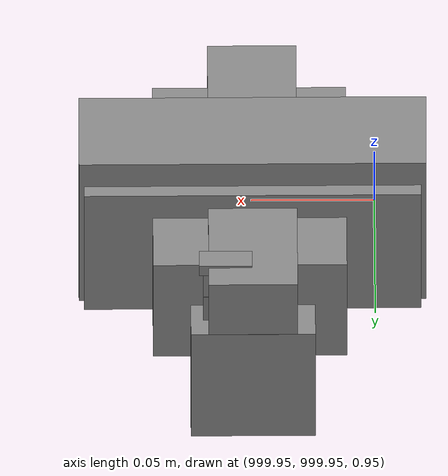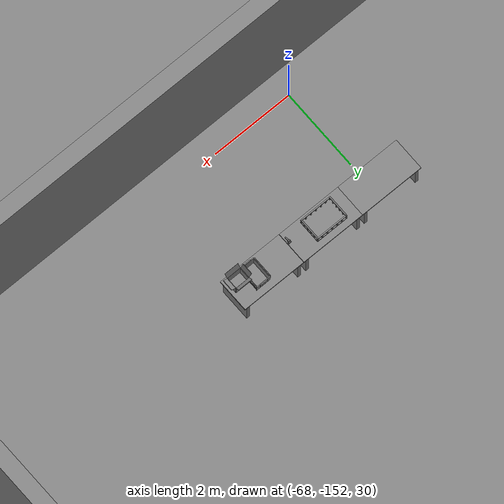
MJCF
<mujoco>
    <option gravity="0.000000000 0.000000000 -9.810000420" timestep="0.0049999999" integrator="implicitfast" density="1.225" viscosity="1.8000001e-05" noslip_iterations="10" iterations="100" sdf_iterations="50">
        <flag multiccd="disable"/>
    </option>
    <size memory="1000M"/>
    <compiler coordinate="local"/>
    <worldbody>
        <light cutoff="30" pos="0 1 1" dir="0 -1 -2"/>
        <light cutoff="30" pos="0 -1 1" dir="0 1 -2"/>
        <body pos="-64.866622925 -149.383972168 30.183746338" euler="89.999984741 89.999946594 0.000000000" name="openloong_gripper_2f85_fix_base_usda_bluebox_01">
            <geom contype="1" conaffinity="1" density="1000" type="box" material="" rgba="0.500000000 0.500000000 0.500000000 1.000000000" solimp="0.899999976 0.949999988 0.001000000" friction="1.000000000 0.005000000 0.000100000" solref="0.020000000 1.000000000" margin="0" condim="3" group="0" pos="0.276580811 0.187225342 0.000068665" quat="0.707106948 0.000077471 0.707106352 0.000077486" size="0.100000001 0.057999998 0.010000000" name="openloong_gripper_2f85_fix_base_usda_geom_14618FB0_1214_4C5E_A9E6_392BC4A86091"/>
            <geom contype="1" conaffinity="1" density="1000" type="box" material="" rgba="0.500000000 0.500000000 0.500000000 1.000000000" solimp="0.899999976 0.949999988 0.001000000" friction="1.000000000 0.005000000 0.000100000" solref="0.020000000 1.000000000" margin="0" condim="3" group="0" pos="0.000000000 0.002883911 0.000000000" quat="0.999999881 0.000000000 0.000000000 0.000000000" size="0.254000008 0.003000000 0.172000006" name="openloong_gripper_2f85_fix_base_usda_geom_357FAF24_0E3C_4D5D_9414_332FA9F2DD39"/>
            <geom contype="1" conaffinity="1" density="1000" type="box" material="" rgba="0.500000000 0.500000000 0.500000000 1.000000000" solimp="0.899999976 0.949999988 0.001000000" friction="1.000000000 0.005000000 0.000100000" solref="0.020000000 1.000000000" margin="0" condim="3" group="0" pos="0.000000000 0.124874115 0.173484802" quat="0.999796331 0.020176515 -0.000000015 0.000000030" size="0.259999990 0.119999997 0.007000000" name="openloong_gripper_2f85_fix_base_usda_geom_6B46461C_8B1F_404C_88EC_25592EA29EB5"/>
            <geom contype="1" conaffinity="1" density="1000" type="box" material="" rgba="0.500000000 0.500000000 0.500000000 1.000000000" solimp="0.899999976 0.949999988 0.001000000" friction="1.000000000 0.005000000 0.000100000" solref="0.020000000 1.000000000" margin="0" condim="3" group="0" pos="0.000000000 0.124874115 -0.173469543" quat="0.999796331 -0.020176545 -0.000000015 0.000000000" size="0.259999990 0.119999997 0.007000000" name="openloong_gripper_2f85_fix_base_usda_geom_AB00E6F2_D0D6_44AA_BF53_B830CE4CDE10"/>
            <geom contype="1" conaffinity="1" density="1000" type="box" material="" rgba="0.500000000 0.500000000 0.500000000 1.000000000" solimp="0.899999976 0.949999988 0.001000000" friction="1.000000000 0.005000000 0.000100000" solref="0.020000000 1.000000000" margin="0" condim="3" group="0" pos="0.000000000 0.214008331 0.188980103" quat="0.999912977 0.013176724 0.000000015 0.000000000" size="0.259999990 0.029999999 0.012500000" name="openloong_gripper_2f85_fix_base_usda_geom_60B22BE7_8701_4418_8490_322968845D00"/>
            <geom contype="1" conaffinity="1" density="1000" type="box" material="" rgba="0.500000000 0.500000000 0.500000000 1.000000000" solimp="0.899999976 0.949999988 0.001000000" friction="1.000000000 0.005000000 0.000100000" solref="0.020000000 1.000000000" margin="0" condim="3" group="0" pos="-0.258361816 0.125289917 0.001876831" quat="0.702796936 -0.020792112 0.710783124 0.020769298" size="0.189999998 0.119999997 0.009000000" name="openloong_gripper_2f85_fix_base_usda_geom_3582B3E8_6956_4603_B027_856481192B31"/>
            <geom contype="1" conaffinity="1" density="1000" type="box" material="" rgba="0.500000000 0.500000000 0.500000000 1.000000000" solimp="0.899999976 0.949999988 0.001000000" friction="1.000000000 0.005000000 0.000100000" solref="0.020000000 1.000000000" margin="0" condim="3" group="0" pos="0.000000000 0.214008331 -0.188980103" quat="0.999912977 -0.013176769 0.000000030 0.000000015" size="0.259999990 0.029999999 0.012500000" name="openloong_gripper_2f85_fix_base_usda_geom_7752D114_2A27_4970_833D_2389B13DA842"/>
            <geom contype="1" conaffinity="1" density="1000" type="box" material="" rgba="0.500000000 0.500000000 0.500000000 1.000000000" solimp="0.899999976 0.949999988 0.001000000" friction="1.000000000 0.005000000 0.000100000" solref="0.020000000 1.000000000" margin="0" condim="3" group="0" pos="-0.276611328 0.187225342 0.000068665" quat="0.707106650 0.000077441 0.707106709 0.000077456" size="0.100000001 0.057999998 0.010000000" name="openloong_gripper_2f85_fix_base_usda_geom_FDFC939D_DCE6_4E07_B7BE_EDE8F9238FE6"/>
            <geom contype="1" conaffinity="1" density="1000" type="box" material="" rgba="0.500000000 0.500000000 0.500000000 1.000000000" solimp="0.899999976 0.949999988 0.001000000" friction="1.000000000 0.005000000 0.000100000" solref="0.020000000 1.000000000" margin="0" condim="3" group="0" pos="0.258331299 0.125289917 0.001876831" quat="0.702851415 0.018856421 0.710823774 -0.019329369" size="0.189999998 0.119999997 0.009000000" name="openloong_gripper_2f85_fix_base_usda_geom_08671940_DFB1_46A4_9BD1_6294B1C78931"/>
            <freejoint name="openloong_gripper_2f85_fix_base_usda_bluebox_01_joint"/>
            <site size="0.005000000 0.005000000 0.005000000" rgba="0.500000000 0.500000000 0.500000000 1.000000000" pos="0.000000000 0.000000000 0.000000000" quat="0.999961913 0.008726534 0.000000000 0.000000000" group="0" type="sphere" name="openloong_gripper_2f85_fix_base_usda_bluebox_01site"/>
        </body>
        <body pos="-64.496299744 -149.491867065 30.235729218" euler="0.000000000 0.000000000 89.999946594" name="openloong_gripper_2f85_fix_base_usda_cardboardbox_01">
            <geom contype="1" conaffinity="1" density="1000" type="box" material="" rgba="0.500000000 0.500000000 0.500000000 1.000000000" solimp="0.899999976 0.949999988 0.001000000" friction="1.000000000 0.005000000 0.000100000" solref="0.020000000 1.000000000" margin="0" condim="3" group="0" pos="-0.003166199 -0.004086494 0.005052090" quat="1.000000000 0.000000000 0.000000000 0.000000000" size="0.142499998 0.177500010 0.005000000" name="openloong_gripper_2f85_fix_base_usda_geom_4A6C3AE8_1232_48D5_B04B_E68928F516CC"/>
            <geom contype="1" conaffinity="1" density="1000" type="box" material="" rgba="0.500000000 0.500000000 0.500000000 1.000000000" solimp="0.899999976 0.949999988 0.001000000" friction="1.000000000 0.005000000 0.000100000" solref="0.020000000 1.000000000" margin="0" condim="3" group="0" pos="-0.003166199 0.170316696 0.150570869" quat="1.000000000 0.000000000 0.000000000 0.000000000" size="0.142499998 0.005000000 0.149999991" name="openloong_gripper_2f85_fix_base_usda_geom_511EAB19_2DE3_43DB_B44E_249537591FC4"/>
            <geom contype="1" conaffinity="1" density="1000" type="box" material="" rgba="0.500000000 0.500000000 0.500000000 1.000000000" solimp="0.899999976 0.949999988 0.001000000" friction="1.000000000 0.005000000 0.000100000" solref="0.020000000 1.000000000" margin="0" condim="3" group="0" pos="-0.147399902 -0.005307198 0.150570869" quat="1.000000000 0.000000000 0.000000000 0.000000000" size="0.005000000 0.177500010 0.149999991" name="openloong_gripper_2f85_fix_base_usda_geom_56CE85D1_F78D_4780_9FBC_47CB1339DDAD"/>
            <geom contype="1" conaffinity="1" density="1000" type="box" material="" rgba="0.500000000 0.500000000 0.500000000 1.000000000" solimp="0.899999976 0.949999988 0.001000000" friction="1.000000000 0.005000000 0.000100000" solref="0.020000000 1.000000000" margin="0" condim="3" group="0" pos="0.140275955 -0.005307198 0.150570869" quat="1.000000000 0.000000000 0.000000000 0.000000000" size="0.005000000 0.177500010 0.149999991" name="openloong_gripper_2f85_fix_base_usda_geom_D0E307D5_DCE8_40E2_BBE5_D4DD435AC261"/>
            <geom contype="1" conaffinity="1" density="1000" type="box" material="" rgba="0.500000000 0.500000000 0.500000000 1.000000000" solimp="0.899999976 0.949999988 0.001000000" friction="1.000000000 0.005000000 0.000100000" solref="0.020000000 1.000000000" margin="0" condim="3" group="0" pos="-0.003166199 -0.181550980 0.150570869" quat="1.000000000 0.000000000 0.000000000 0.000000000" size="0.142499998 0.005000000 0.149999991" name="openloong_gripper_2f85_fix_base_usda_geom_EB2A08C8_8580_47B8_A7D5_FD163269F0C6"/>
            <freejoint name="openloong_gripper_2f85_fix_base_usda_cardboardbox_01_joint"/>
            <site size="0.005000000 0.005000000 0.005000000" rgba="0.500000000 0.500000000 0.500000000 1.000000000" pos="0.000000000 0.000000000 0.000000000" quat="0.999961913 0.008726535 0.000000000 0.000000000" group="0" type="sphere" name="openloong_gripper_2f85_fix_base_usda_site_8E293B6C_25B9_4F91_A9CB_243C47A997ED"/>
            <body pos="0.139160156 -0.004048347 0.301930904" euler="-179.999954224 49.383502960 179.999954224" name="openloong_gripper_2f85_fix_base_usda_A1_006">
                <geom contype="1" conaffinity="1" density="1000" type="box" material="" rgba="0.500000000 0.500000000 0.500000000 1.000000000" solimp="0.899999976 0.949999988 0.001000000" friction="1.000000000 0.005000000 0.000100000" solref="0.020000000 1.000000000" margin="0" condim="3" group="0" pos="-0.071587563 0.000009537 0.001745224" quat="0.999999881 0.000000000 0.000000000 0.000000000" size="0.071249999 0.179999992 0.002500000" name="openloong_gripper_2f85_fix_base_usda_geom_16093634_0575_4FFB_9FE4_61B87E2FEF56"/>
                <joint armature="0" stiffness="0.07" damping="0.0099999998" axis="0.000000 1.000000 0.000000" type="hinge" name="openloong_gripper_2f85_fix_base_usda_A1_006"/>
            </body>
            <body pos="-0.145902634 -0.004086494 0.301938057" euler="-180.000000000 -60.000011444 -180.000000000" name="openloong_gripper_2f85_fix_base_usda_A2_006">
                <geom contype="1" conaffinity="1" density="1000" type="box" material="" rgba="0.500000000 0.500000000 0.500000000 1.000000000" solimp="0.899999976 0.949999988 0.001000000" friction="1.000000000 0.005000000 0.000100000" solref="0.020000000 1.000000000" margin="0" condim="3" group="0" pos="0.071268082 0.000009537 0.002717972" quat="0.000002921 0.000000000 -0.000000030 0.999999881" size="0.071249999 0.179999992 0.002500000" name="openloong_gripper_2f85_fix_base_usda_geom_2ADDDD24_B915_4D7D_994E_E16864ED56BC"/>
                <joint armature="0" stiffness="0.07" damping="0.0099999998" axis="0.000000 1.000000 0.000000" type="hinge" name="openloong_gripper_2f85_fix_base_usda_A2_006"/>
            </body>
            <body pos="-0.003385544 0.175991058 0.301930904" euler="-125.858116150 -0.000004561 0.000002331" name="openloong_gripper_2f85_fix_base_usda_B2_006">
                <geom contype="1" conaffinity="1" density="1000" type="box" material="" rgba="0.500000000 0.500000000 0.500000000 1.000000000" solimp="0.899999976 0.949999988 0.001000000" friction="1.000000000 0.005000000 0.000100000" solref="0.020000000 1.000000000" margin="0" condim="3" group="0" pos="0.000009537 -0.070939064 -0.002470016" quat="0.999614120 0.027776197 -0.000000015 0.000000030" size="0.137500003 0.064999998 0.005000000" name="openloong_gripper_2f85_fix_base_usda_geom_15572F49_F6F2_44E7_9F90_6E757ED61C44"/>
                <joint armature="0" stiffness="0.07" damping="0.0099999998" axis="1.000000 0.000000 0.000000" type="hinge" name="openloong_gripper_2f85_fix_base_usda_B2_006"/>
            </body>
            <body pos="-0.003385544 -0.184140205 0.301938057" euler="147.805557251 0.000000000 0.000000000" name="openloong_gripper_2f85_fix_base_usda_B1_006">
                <geom contype="1" conaffinity="1" density="1000" type="box" material="" rgba="0.500000000 0.500000000 0.500000000 1.000000000" solimp="0.899999976 0.949999988 0.001000000" friction="1.000000000 0.005000000 0.000100000" solref="0.020000000 1.000000000" margin="0" condim="3" group="0" pos="-0.000028610 0.070202351 -0.002703667" quat="0.999614179 -0.027776167 0.000000000 0.000000000" size="0.137500003 0.064999998 0.005000000" name="openloong_gripper_2f85_fix_base_usda_geom_740A8399_A7AE_4197_A859_786601C3133D"/>
                <joint armature="0" stiffness="0.07" damping="0.0099999998" axis="1.000000 0.000000 0.000000" type="hinge" name="openloong_gripper_2f85_fix_base_usda_B1_006"/>
            </body>
        </body>
        <body pos="-65.882858276 -149.481979370 30.229999542" euler="-64.487716675 0.000000000 0.000000000" name="openloong_gripper_2f85_fix_base_usda_Barcode">
            <geom contype="1" conaffinity="1" density="1000" type="box" material="" rgba="0.500000000 0.500000000 0.500000000 1.000000000" solimp="0.899999976 0.949999988 0.001000000" friction="1.000000000 0.005000000 0.000100000" solref="0.020000000 1.000000000" margin="0" condim="3" group="0" pos="0.000000000 0.013038635 0.001419067" quat="0.000000000 0.000000000 0.000000000 1.000000119" size="0.034000002 0.010000000 0.017999999" name="openloong_gripper_2f85_fix_base_usda_geom_2B55BC46_7D6E_4486_B14D_FEDB79FB5A83"/>
            <geom contype="1" conaffinity="1" density="1000" type="box" material="" rgba="0.500000000 0.500000000 0.500000000 1.000000000" solimp="0.899999976 0.949999988 0.001000000" friction="1.000000000 0.005000000 0.000100000" solref="0.020000000 1.000000000" margin="0" condim="3" group="0" pos="0.000000000 -0.035301208 -0.007095337" quat="0.000000000 0.000000000 -0.043619365 0.999048233" size="0.028999999 0.010000000 0.020000000" name="openloong_gripper_2f85_fix_base_usda_geom_898560AD_9C34_4E92_A55C_B7F0A20CE94A"/>
            <geom contype="1" conaffinity="1" density="1000" type="box" material="" rgba="0.500000000 0.500000000 0.500000000 1.000000000" solimp="0.899999976 0.949999988 0.001000000" friction="1.000000000 0.005000000 0.000100000" solref="0.020000000 1.000000000" margin="0" condim="3" group="0" pos="0.000000000 -0.043411255 -0.011749268" quat="0.922262907 0.386563420 0.000000000 0.000000000" size="0.026000001 0.010000000 0.020000000" name="openloong_gripper_2f85_fix_base_usda_geom_33A0BC9C_0508_4F18_96CA_85F163FFC2A6"/>
            <geom contype="1" conaffinity="1" density="1000" type="box" material="" rgba="0.500000000 0.500000000 0.500000000 1.000000000" solimp="0.899999976 0.949999988 0.001000000" friction="1.000000000 0.005000000 0.000100000" solref="0.020000000 1.000000000" margin="0" condim="3" group="0" pos="0.000000000 -0.016967773 -0.031860352" quat="0.000000000 0.000000000 0.000000000 1.000000119" size="0.008000000 0.010000000 0.013000000" name="openloong_gripper_2f85_fix_base_usda_geom_84D4159B_9326_49FF_A598_4AB7901BB255"/>
            <geom contype="1" conaffinity="1" density="1000" type="box" material="" rgba="0.500000000 0.500000000 0.500000000 1.000000000" solimp="0.899999976 0.949999988 0.001000000" friction="1.000000000 0.005000000 0.000100000" solref="0.020000000 1.000000000" margin="0" condim="3" group="0" pos="0.000000000 -0.001869202 0.000312805" quat="0.953716993 0.300705761 0.000000000 0.000000000" size="0.032000002 0.010000000 0.018999999" name="openloong_gripper_2f85_fix_base_usda_geom_FE839CA9_0745_4B12_8B81_D4A3FDA5B93B"/>
            <geom contype="1" conaffinity="1" density="1000" type="box" material="" rgba="0.500000000 0.500000000 0.500000000 1.000000000" solimp="0.899999976 0.949999988 0.001000000" friction="1.000000000 0.005000000 0.000100000" solref="0.020000000 1.000000000" margin="0" condim="3" group="0" pos="0.000000000 -0.019531250 -0.003173828" quat="0.953716993 0.300705761 0.000000000 0.000000000" size="0.030999999 0.010000000 0.020000000" name="openloong_gripper_2f85_fix_base_usda_geom_FFAA176B_D63C_4364_9F47_DF065CDE6950"/>
            <geom contype="1" conaffinity="1" density="1000" type="box" material="" rgba="0.500000000 0.500000000 0.500000000 1.000000000" solimp="0.899999976 0.949999988 0.001000000" friction="1.000000000 0.005000000 0.000100000" solref="0.020000000 1.000000000" margin="0" condim="3" group="0" pos="0.000000000 -0.035301208 -0.007095337" quat="0.953716993 0.300705761 0.000000000 0.000000000" size="0.028999999 0.010000000 0.020000000" name="openloong_gripper_2f85_fix_base_usda_geom_01E7C1AF_2CF6_4E5C_A6AA_D408A86F501B"/>
            <geom contype="1" conaffinity="1" density="1000" type="box" material="" rgba="0.500000000 0.500000000 0.500000000 1.000000000" solimp="0.899999976 0.949999988 0.001000000" friction="1.000000000 0.005000000 0.000100000" solref="0.020000000 1.000000000" margin="0" condim="3" group="0" pos="0.000000000 -0.042617798 -0.071121216" quat="0.000000000 0.000000000 0.000000000 1.000000119" size="0.013000000 0.021000000 0.059999999" name="openloong_gripper_2f85_fix_base_usda_geom_A8555863_5D97_4E3D_A30D_13D3B5ED4451"/>
            <freejoint name="openloong_gripper_2f85_fix_base_usda_Barcode_joint"/>
            <site size="0.005000000 0.005000000 0.005000000" rgba="0.500000000 0.500000000 0.500000000 1.000000000" pos="0.000000000 0.000000000 0.000000000" quat="1.000000000 0.000000000 0.000000000 0.000000000" group="0" type="sphere" name="openloong_gripper_2f85_fix_base_usda_Barcode_site"/>
        </body>
        <body pos="-66.745018005 -149.392349243 30.184000015" euler="0.000000000 0.000000000 89.999946594" name="[22329653452018]_Basket_01">
            <geom contype="1" conaffinity="1" density="1000" type="box" material="" rgba="0.500000000 0.500000000 0.500000000 1.000000000" solimp="0.899999976 0.949999988 0.001000000" friction="1.000000000 0.005000000 0.000100000" solref="0.020000000 1.000000000" margin="0" condim="3" group="0" pos="-0.052425385 0.389207840 0.089787483" quat="0.707107008 0.000000000 0.000000000 0.707106411" size="0.014249999 0.014249999 0.059999999" name="[22329653452018]_geom_1A7758FC_8F1D_4BD6_AD75_57F01B5367B8"/>
            <geom contype="1" conaffinity="1" density="1000" type="box" material="" rgba="0.500000000 0.500000000 0.500000000 1.000000000" solimp="0.899999976 0.949999988 0.001000000" friction="1.000000000 0.005000000 0.000100000" solref="0.020000000 1.000000000" margin="0" condim="3" group="0" pos="0.264015198 -0.133043289 0.089787483" quat="0.707107008 0.000000000 0.000000000 0.707106411" size="0.014249999 0.014249999 0.059999999" name="[22329653452018]_geom_35B0C24D_67C4_4BDD_B5DD_5F8680D9276E"/>
            <geom contype="1" conaffinity="1" density="1000" type="box" material="" rgba="0.500000000 0.500000000 0.500000000 1.000000000" solimp="0.899999976 0.949999988 0.001000000" friction="1.000000000 0.005000000 0.000100000" solref="0.020000000 1.000000000" margin="0" condim="3" group="0" pos="-0.264015198 -0.265548706 0.089793205" quat="0.707107008 0.000000000 0.000000000 0.707106411" size="0.014249999 0.014249999 0.059999999" name="[22329653452018]_geom_D6CC5F78_FD24_433D_9703_C128A90BFA79"/>
            <geom contype="1" conaffinity="1" density="1000" type="box" material="" rgba="0.500000000 0.500000000 0.500000000 1.000000000" solimp="0.899999976 0.949999988 0.001000000" friction="1.000000000 0.005000000 0.000100000" solref="0.020000000 1.000000000" margin="0" condim="3" group="0" pos="-0.160263062 -0.389322281 0.089793205" quat="0.707107008 0.000000000 0.000000000 0.707106411" size="0.014249999 0.014249999 0.059999999" name="[22329653452018]_geom_CDE2A584_4E77_481B_8B1B_82ABFF6312B8"/>
            <geom contype="1" conaffinity="1" density="1000" type="box" material="" rgba="0.500000000 0.500000000 0.500000000 1.000000000" solimp="0.899999976 0.949999988 0.001000000" friction="1.000000000 0.005000000 0.000100000" solref="0.020000000 1.000000000" margin="0" condim="3" group="0" pos="0.162265778 -0.389322281 0.089787483" quat="0.707107008 0.000000000 0.000000000 0.707106411" size="0.014249999 0.014249999 0.059999999" name="[22329653452018]_geom_31444B8F_2FC8_4012_8B4F_D27CB6C50F59"/>
            <geom contype="1" conaffinity="1" density="1000" type="box" material="" rgba="0.500000000 0.500000000 0.500000000 1.000000000" solimp="0.899999976 0.949999988 0.001000000" friction="1.000000000 0.005000000 0.000100000" solref="0.020000000 1.000000000" margin="0" condim="3" group="0" pos="0.264015198 0.389207840 0.089787483" quat="0.707107008 0.000000000 0.000000000 0.707106411" size="0.014249999 0.014249999 0.059999999" name="[22329653452018]_geom_1EBE2EDC_F00A_400B_AD6B_9E76C9D968D8"/>
            <geom contype="1" conaffinity="1" density="1000" type="box" material="" rgba="0.500000000 0.500000000 0.500000000 1.000000000" solimp="0.899999976 0.949999988 0.001000000" friction="1.000000000 0.005000000 0.000100000" solref="0.020000000 1.000000000" margin="0" condim="3" group="0" pos="-0.264015198 -0.133043289 0.089793205" quat="0.707107008 0.000000000 0.000000000 0.707106411" size="0.014249999 0.014249999 0.059999999" name="[22329653452018]_geom_D20EDD30_F81A_41C9_B0A7_AED182D5B563"/>
            <geom contype="1" conaffinity="1" density="1000" type="box" material="" rgba="0.500000000 0.500000000 0.500000000 1.000000000" solimp="0.899999976 0.949999988 0.001000000" friction="1.000000000 0.005000000 0.000100000" solref="0.020000000 1.000000000" margin="0" condim="3" group="0" pos="-0.264026642 0.269256592 0.089793205" quat="0.707107008 0.000000000 0.000000000 0.707106411" size="0.014249999 0.014249999 0.059999999" name="[22329653452018]_geom_0C3EF6E0_AB8B_4878_84C6_ACACF8FCE2EF"/>
            <geom contype="1" conaffinity="1" density="1000" type="box" material="" rgba="0.500000000 0.500000000 0.500000000 1.000000000" solimp="0.899999976 0.949999988 0.001000000" friction="1.000000000 0.005000000 0.000100000" solref="0.020000000 1.000000000" margin="0" condim="3" group="0" pos="0.054462433 0.389207840 0.089787483" quat="0.707107008 0.000000000 0.000000000 0.707106411" size="0.014249999 0.014249999 0.059999999" name="[22329653452018]_geom_52D10153_64A7_4888_99EC_148AF11F66E5"/>
            <geom contype="1" conaffinity="1" density="1000" type="box" material="" rgba="0.500000000 0.500000000 0.500000000 1.000000000" solimp="0.899999976 0.949999988 0.001000000" friction="1.000000000 0.005000000 0.000100000" solref="0.020000000 1.000000000" margin="0" condim="3" group="0" pos="0.054462433 -0.389322281 0.089787483" quat="0.707107008 0.000000000 0.000000000 0.707106411" size="0.014249999 0.014249999 0.059999999" name="[22329653452018]_geom_69754928_F75D_4868_BE97_3D0F9F285C31"/>
            <geom contype="1" conaffinity="1" density="1000" type="box" material="" rgba="0.500000000 0.500000000 0.500000000 1.000000000" solimp="0.899999976 0.949999988 0.001000000" friction="1.000000000 0.005000000 0.000100000" solref="0.020000000 1.000000000" margin="0" condim="3" group="0" pos="0.264015198 0.269256592 0.089793205" quat="0.707107008 0.000000000 0.000000000 0.707106411" size="0.014249999 0.014249999 0.059999999" name="[22329653452018]_geom_88CDE4CA_B09B_485F_812F_DB4C1E195825"/>
            <geom contype="1" conaffinity="1" density="1000" type="box" material="" rgba="0.500000000 0.500000000 0.500000000 1.000000000" solimp="0.899999976 0.949999988 0.001000000" friction="1.000000000 0.005000000 0.000100000" solref="0.020000000 1.000000000" margin="0" condim="3" group="0" pos="0.264015198 -0.389322281 0.089787483" quat="0.707107008 0.000000000 0.000000000 0.707106411" size="0.014249999 0.014249999 0.059999999" name="[22329653452018]_geom_BC37F7C5_8230_4174_AC36_BAD0D16E0DCF"/>
            <geom contype="1" conaffinity="1" density="1000" type="box" material="" rgba="0.500000000 0.500000000 0.500000000 1.000000000" solimp="0.899999976 0.949999988 0.001000000" friction="1.000000000 0.005000000 0.000100000" solref="0.020000000 1.000000000" margin="0" condim="3" group="0" pos="0.000000000 0.000000000 0.015998840" quat="0.707107008 0.000000000 0.000000000 0.707106411" size="0.403499991 0.279000014 0.015750000" name="[22329653452018]_geom_B563A397_D23B_4945_8F77_62FCE09E597A"/>
            <geom contype="1" conaffinity="1" density="1000" type="box" material="" rgba="0.500000000 0.500000000 0.500000000 1.000000000" solimp="0.899999976 0.949999988 0.001000000" friction="1.000000000 0.005000000 0.000100000" solref="0.020000000 1.000000000" margin="0" condim="3" group="0" pos="0.000000000 -0.389476776 0.163619041" quat="0.707107008 0.000000000 0.000000000 0.707106411" size="0.015000000 0.277500004 0.015750000" name="[22329653452018]_geom_0993D44B_953D_4BDD_881E_22DADFFD5C99"/>
            <geom contype="1" conaffinity="1" density="1000" type="box" material="" rgba="0.500000000 0.500000000 0.500000000 1.000000000" solimp="0.899999976 0.949999988 0.001000000" friction="1.000000000 0.005000000 0.000100000" solref="0.020000000 1.000000000" margin="0" condim="3" group="0" pos="0.162265778 0.389207840 0.089787483" quat="0.707107008 0.000000000 0.000000000 0.707106411" size="0.014249999 0.014249999 0.059999999" name="[22329653452018]_geom_46320F7B_0F04_4231_AB21_004DC4A62D18"/>
            <geom contype="1" conaffinity="1" density="1000" type="box" material="" rgba="0.500000000 0.500000000 0.500000000 1.000000000" solimp="0.899999976 0.949999988 0.001000000" friction="1.000000000 0.005000000 0.000100000" solref="0.020000000 1.000000000" margin="0" condim="3" group="0" pos="0.000000000 0.389471054 0.163619041" quat="0.707107008 0.000000000 0.000000000 0.707106411" size="0.015000000 0.277500004 0.015750000" name="[22329653452018]_geom_3160C53D_76E2_41F9_B6F2_7F61458F46F9"/>
            <geom contype="1" conaffinity="1" density="1000" type="box" material="" rgba="0.500000000 0.500000000 0.500000000 1.000000000" solimp="0.899999976 0.949999988 0.001000000" friction="1.000000000 0.005000000 0.000100000" solref="0.020000000 1.000000000" margin="0" condim="3" group="0" pos="-0.263511658 0.000000000 0.163619041" quat="0.707107008 0.000000000 0.000000000 0.707106411" size="0.403499991 0.015000000 0.015750000" name="[22329653452018]_geom_97B70934_4730_42F7_BFA4_6ED6F8394997"/>
            <geom contype="1" conaffinity="1" density="1000" type="box" material="" rgba="0.500000000 0.500000000 0.500000000 1.000000000" solimp="0.899999976 0.949999988 0.001000000" friction="1.000000000 0.005000000 0.000100000" solref="0.020000000 1.000000000" margin="0" condim="3" group="0" pos="-0.264015198 0.141334534 0.089793205" quat="0.707107008 0.000000000 0.000000000 0.707106411" size="0.014249999 0.014249999 0.059999999" name="[22329653452018]_geom_A3A60A2D_D930_453A_B03A_D1140DBD55F6"/>
            <geom contype="1" conaffinity="1" density="1000" type="box" material="" rgba="0.500000000 0.500000000 0.500000000 1.000000000" solimp="0.899999976 0.949999988 0.001000000" friction="1.000000000 0.005000000 0.000100000" solref="0.020000000 1.000000000" margin="0" condim="3" group="0" pos="0.264015198 -0.265548706 0.089787483" quat="0.707107008 0.000000000 0.000000000 0.707106411" size="0.014249999 0.014249999 0.059999999" name="[22329653452018]_geom_2EA72446_55F5_461A_90F7_C3A6409FB239"/>
            <geom contype="1" conaffinity="1" density="1000" type="box" material="" rgba="0.500000000 0.500000000 0.500000000 1.000000000" solimp="0.899999976 0.949999988 0.001000000" friction="1.000000000 0.005000000 0.000100000" solref="0.020000000 1.000000000" margin="0" condim="3" group="0" pos="-0.160263062 0.389207840 0.089787483" quat="0.707107008 0.000000000 0.000000000 0.707106411" size="0.014249999 0.014249999 0.059999999" name="[22329653452018]_geom_075A53B0_FBF9_47EA_88DB_28D252633728"/>
            <geom contype="1" conaffinity="1" density="1000" type="box" material="" rgba="0.500000000 0.500000000 0.500000000 1.000000000" solimp="0.899999976 0.949999988 0.001000000" friction="1.000000000 0.005000000 0.000100000" solref="0.020000000 1.000000000" margin="0" condim="3" group="0" pos="-0.052425385 -0.389322281 0.089787483" quat="0.707107008 0.000000000 0.000000000 0.707106411" size="0.014249999 0.014249999 0.059999999" name="[22329653452018]_geom_FD366DDA_4ED6_4DC3_8943_A7DF378EB055"/>
            <geom contype="1" conaffinity="1" density="1000" type="box" material="" rgba="0.500000000 0.500000000 0.500000000 1.000000000" solimp="0.899999976 0.949999988 0.001000000" friction="1.000000000 0.005000000 0.000100000" solref="0.020000000 1.000000000" margin="0" condim="3" group="0" pos="-0.264026642 -0.389322281 0.089793205" quat="0.707107008 0.000000000 0.000000000 0.707106411" size="0.014249999 0.014249999 0.059999999" name="[22329653452018]_geom_4C824A4B_D7C0_484E_9237_8B94C60BBF62"/>
            <geom contype="1" conaffinity="1" density="1000" type="box" material="" rgba="0.500000000 0.500000000 0.500000000 1.000000000" solimp="0.899999976 0.949999988 0.001000000" friction="1.000000000 0.005000000 0.000100000" solref="0.020000000 1.000000000" margin="0" condim="3" group="0" pos="0.264015198 0.141334534 0.089787483" quat="0.707107008 0.000000000 0.000000000 0.707106411" size="0.014249999 0.014249999 0.059999999" name="[22329653452018]_geom_90AF2590_3DC7_417F_96B2_878AD44FC693"/>
            <geom contype="1" conaffinity="1" density="1000" type="box" material="" rgba="0.500000000 0.500000000 0.500000000 1.000000000" solimp="0.899999976 0.949999988 0.001000000" friction="1.000000000 0.005000000 0.000100000" solref="0.020000000 1.000000000" margin="0" condim="3" group="0" pos="-0.264015198 0.389207840 0.089793205" quat="0.707107008 0.000000000 0.000000000 0.707106411" size="0.014249999 0.014249999 0.059999999" name="[22329653452018]_geom_911DD865_00C2_4CCF_8E8D_8605D22D6FE5"/>
            <geom contype="1" conaffinity="1" density="1000" type="box" material="" rgba="0.500000000 0.500000000 0.500000000 1.000000000" solimp="0.899999976 0.949999988 0.001000000" friction="1.000000000 0.005000000 0.000100000" solref="0.020000000 1.000000000" margin="0" condim="3" group="0" pos="0.264015198 0.004480362 0.089787483" quat="0.707107008 0.000000000 0.000000000 0.707106411" size="0.014249999 0.014249999 0.059999999" name="[22329653452018]_geom_A2878362_ACBC_40A8_A66C_4C113A767881"/>
            <geom contype="1" conaffinity="1" density="1000" type="box" material="" rgba="0.500000000 0.500000000 0.500000000 1.000000000" solimp="0.899999976 0.949999988 0.001000000" friction="1.000000000 0.005000000 0.000100000" solref="0.020000000 1.000000000" margin="0" condim="3" group="0" pos="0.263694763 -0.000011444 0.163619041" quat="0.707107008 0.000000000 0.000000000 0.707106411" size="0.403499991 0.015000000 0.015750000" name="[22329653452018]_geom_D65F0F6C_E5EF_4E6F_BD3F_A026036C08F6"/>
            <geom contype="1" conaffinity="1" density="1000" type="box" material="" rgba="0.500000000 0.500000000 0.500000000 1.000000000" solimp="0.899999976 0.949999988 0.001000000" friction="1.000000000 0.005000000 0.000100000" solref="0.020000000 1.000000000" margin="0" condim="3" group="0" pos="-0.264015198 0.004480362 0.089793205" quat="0.707107008 0.000000000 0.000000000 0.707106411" size="0.014249999 0.014249999 0.059999999" name="[22329653452018]_geom_79A6AABA_7E95_408C_A21B_B711A6835FE1"/>
            <freejoint name="[22329653452018]_joint_17ADB4AD_03CC_4856_B2CF_D58A7A3E6F7E"/>
        </body>
        <body pos="0.000000000 0.000000000 0.000000000" euler="0.000000000 0.000000000 0.000000000" name="Static Objects_Static Objects">
            <geom contype="1" conaffinity="1" density="1000" type="box" material="" rgba="0.500000000 0.500000000 0.500000000 1.000000000" solimp="0.899999976 0.949999988 0.001000000" friction="1.000000000 0.005000000 0.000100000" solref="0.020000000 1.000000000" margin="0" condim="3" group="0" pos="-67.544113159 -149.365814209 29.727830887" quat="0.500000417 0.499999970 0.499999553 0.499999970" size="0.381000012 0.319999993 0.041000001" name="Static Objects_geom_3A519458_D12C_4EB5_AF49_3B525502E4FB"/>
            <geom contype="1" conaffinity="1" density="1000" type="box" material="" rgba="0.500000000 0.500000000 0.500000000 1.000000000" solimp="0.899999976 0.949999988 0.001000000" friction="1.000000000 0.005000000 0.000100000" solref="0.020000000 1.000000000" margin="0" condim="3" group="0" pos="-68.239501953 -149.365814209 30.086868286" quat="0.500000417 0.499999970 0.499999553 0.499999970" size="0.370999992 0.039500002 0.745000005" name="Static Objects_geom_1FD18D68_5C8D_4DF4_84FC_91DF90A552D6"/>
            <geom contype="1" conaffinity="1" density="1000" type="box" material="" rgba="0.500000000 0.500000000 0.500000000 1.000000000" solimp="0.899999976 0.949999988 0.001000000" friction="1.000000000 0.005000000 0.000100000" solref="0.020000000 1.000000000" margin="0" condim="3" group="0" pos="-68.239501953 -149.365814209 30.147235870" quat="0.500000417 0.499999970 0.499999553 0.499999970" size="0.400000006 0.022000000 0.800000012" name="Static Objects_geom_F504B0CA_333E_42EB_BE9A_BA5E8A3F9F3D"/>
            <geom contype="1" conaffinity="1" density="1000" type="box" material="" rgba="0.500000000 0.500000000 0.500000000 1.000000000" solimp="0.899999976 0.949999988 0.001000000" friction="1.000000000 0.005000000 0.000100000" solref="0.020000000 1.000000000" margin="0" condim="3" group="0" pos="-68.934890747 -149.365814209 29.727830887" quat="0.500000417 0.499999970 0.499999553 0.499999970" size="0.381000012 0.319999993 0.041000001" name="Static Objects_geom_A52D8EBF_E02C_4D31_A063_34078C7A02D9"/>
            <geom contype="1" conaffinity="1" density="1000" type="box" material="" rgba="0.500000000 0.500000000 0.500000000 1.000000000" solimp="0.899999976 0.949999988 0.001000000" friction="1.000000000 0.005000000 0.000100000" solref="0.020000000 1.000000000" margin="0" condim="3" group="0" pos="-68.239501953 -149.365814209 29.561563492" quat="0.500000417 0.499999970 0.499999553 0.499999970" size="0.020000000 0.022000000 0.660000026" name="Static Objects_geom_C74E5AC4_7560_4333_9F85_1B9F1026C238"/>
            <geom contype="1" conaffinity="1" density="1000" type="box" material="" rgba="0.500000000 0.500000000 0.500000000 1.000000000" solimp="0.899999976 0.949999988 0.001000000" friction="1.000000000 0.005000000 0.000100000" solref="0.020000000 1.000000000" margin="0" condim="3" group="0" pos="-65.945671082 -149.365814209 29.727830887" quat="0.500000417 0.499999970 0.499999553 0.499999970" size="0.381000012 0.319999993 0.041000001" name="Static Objects_geom_D5B3127B_7659_4B28_8E8D_60A70AF73893"/>
            <geom contype="1" conaffinity="1" density="1000" type="box" material="" rgba="0.500000000 0.500000000 0.500000000 1.000000000" solimp="0.899999976 0.949999988 0.001000000" friction="1.000000000 0.005000000 0.000100000" solref="0.020000000 1.000000000" margin="0" condim="3" group="0" pos="-66.641059875 -149.365814209 30.086868286" quat="0.500000417 0.499999970 0.499999553 0.499999970" size="0.370999992 0.039500002 0.745000005" name="Static Objects_geom_87521E74_1759_407A_B216_D0D3CDDC8232"/>
            <geom contype="1" conaffinity="1" density="1000" type="box" material="" rgba="0.500000000 0.500000000 0.500000000 1.000000000" solimp="0.899999976 0.949999988 0.001000000" friction="1.000000000 0.005000000 0.000100000" solref="0.020000000 1.000000000" margin="0" condim="3" group="0" pos="-66.641059875 -149.365814209 30.147235870" quat="0.500000417 0.499999970 0.499999553 0.499999970" size="0.400000006 0.022000000 0.800000012" name="Static Objects_geom_6EB71877_1334_4F96_94DB_001D6A2DDF5E"/>
            <geom contype="1" conaffinity="1" density="1000" type="box" material="" rgba="0.500000000 0.500000000 0.500000000 1.000000000" solimp="0.899999976 0.949999988 0.001000000" friction="1.000000000 0.005000000 0.000100000" solref="0.020000000 1.000000000" margin="0" condim="3" group="0" pos="-67.336448669 -149.365814209 29.727830887" quat="0.500000417 0.499999970 0.499999553 0.499999970" size="0.381000012 0.319999993 0.041000001" name="Static Objects_geom_FBF21B64_12DD_4FB9_9A29_BF6D567F141A"/>
            <geom contype="1" conaffinity="1" density="1000" type="box" material="" rgba="0.500000000 0.500000000 0.500000000 1.000000000" solimp="0.899999976 0.949999988 0.001000000" friction="1.000000000 0.005000000 0.000100000" solref="0.020000000 1.000000000" margin="0" condim="3" group="0" pos="-66.641059875 -149.365814209 29.561563492" quat="0.500000417 0.499999970 0.499999553 0.499999970" size="0.020000000 0.022000000 0.660000026" name="Static Objects_geom_EDDDDDBE_2575_4B3E_B30E_30CE777E2F0B"/>
            <geom contype="1" conaffinity="1" density="1000" type="box" material="" rgba="0.500000000 0.500000000 0.500000000 1.000000000" solimp="0.899999976 0.949999988 0.001000000" friction="1.000000000 0.005000000 0.000100000" solref="0.020000000 1.000000000" margin="0" condim="3" group="0" pos="-64.338577271 -149.365814209 29.727830887" quat="0.500000417 0.499999970 0.499999553 0.499999970" size="0.381000012 0.319999993 0.041000001" name="Static Objects_geom_9EC3BDD4_CC0C_4C60_81C4_E694A4B40F9A"/>
            <geom contype="1" conaffinity="1" density="1000" type="box" material="" rgba="0.500000000 0.500000000 0.500000000 1.000000000" solimp="0.899999976 0.949999988 0.001000000" friction="1.000000000 0.005000000 0.000100000" solref="0.020000000 1.000000000" margin="0" condim="3" group="0" pos="-65.033966064 -149.365814209 30.086868286" quat="0.500000417 0.499999970 0.499999553 0.499999970" size="0.370999992 0.039500002 0.745000005" name="Static Objects_geom_9BB721B2_F7DE_4138_B6F8_0F4028A59654"/>
            <geom contype="1" conaffinity="1" density="1000" type="box" material="" rgba="0.500000000 0.500000000 0.500000000 1.000000000" solimp="0.899999976 0.949999988 0.001000000" friction="1.000000000 0.005000000 0.000100000" solref="0.020000000 1.000000000" margin="0" condim="3" group="0" pos="-65.033966064 -149.365814209 30.147235870" quat="0.500000417 0.499999970 0.499999553 0.499999970" size="0.400000006 0.022000000 0.800000012" name="Static Objects_geom_19FF007D_C6E0_4537_A31A_9ED951FC0B36"/>
            <geom contype="1" conaffinity="1" density="1000" type="box" material="" rgba="0.500000000 0.500000000 0.500000000 1.000000000" solimp="0.899999976 0.949999988 0.001000000" friction="1.000000000 0.005000000 0.000100000" solref="0.020000000 1.000000000" margin="0" condim="3" group="0" pos="-65.729354858 -149.365814209 29.727830887" quat="0.500000417 0.499999970 0.499999553 0.499999970" size="0.381000012 0.319999993 0.041000001" name="Static Objects_geom_F82017DC_E794_4E33_8646_E473F01C3394"/>
            <geom contype="1" conaffinity="1" density="1000" type="box" material="" rgba="0.500000000 0.500000000 0.500000000 1.000000000" solimp="0.899999976 0.949999988 0.001000000" friction="1.000000000 0.005000000 0.000100000" solref="0.020000000 1.000000000" margin="0" condim="3" group="0" pos="-65.033966064 -149.365814209 29.561563492" quat="0.500000417 0.499999970 0.499999553 0.499999970" size="0.020000000 0.022000000 0.660000026" name="Static Objects_geom_539C0180_7B81_4454_AE76_637B331B58D8"/>
            <geom contype="1" conaffinity="1" density="1000" type="box" material="" rgba="0.500000000 0.500000000 0.500000000 1.000000000" solimp="0.899999976 0.949999988 0.001000000" friction="1.000000000 0.005000000 0.000100000" solref="0.020000000 1.000000000" margin="0" condim="3" group="0" pos="-61.754566193 -137.853729248 33.906845093" quat="0.707107067 0.000000000 0.000000000 0.707106471" size="0.759999990 0.759999990 4.500000000" name="Static Objects_geom_B4FE9B5E_3534_45D5_A6E7_1D57338EC0EC"/>
            <geom contype="1" conaffinity="1" density="1000" type="box" material="" rgba="0.500000000 0.500000000 0.500000000 1.000000000" solimp="0.899999976 0.949999988 0.001000000" friction="1.000000000 0.005000000 0.000100000" solref="0.020000000 1.000000000" margin="0" condim="3" group="0" pos="-57.511135101 -144.927108765 31.707921982" quat="1.000000000 0.000000000 0.000000000 0.000000000" size="0.200000003 8.000000000 2.299999952" name="Static Objects_geom_D0CF7053_A40A_461E_85E4_1729D0AD8546"/>
            <geom contype="1" conaffinity="1" density="1000" type="box" material="" rgba="0.500000000 0.500000000 0.500000000 1.000000000" solimp="0.899999976 0.949999988 0.001000000" friction="1.000000000 0.005000000 0.000100000" solref="0.020000000 1.000000000" margin="0" condim="3" group="0" pos="-80.517646790 -157.574050903 31.688196182" quat="0.707107067 0.000000000 0.000000000 0.707106471" size="0.600000024 0.600000024 2.299999952" name="Static Objects_geom_233727F6_EE69_459F_A8F1_6475D6DC6453"/>
            <geom contype="1" conaffinity="1" density="1000" type="box" material="" rgba="0.500000000 0.500000000 0.500000000 1.000000000" solimp="0.899999976 0.949999988 0.001000000" friction="1.000000000 0.005000000 0.000100000" solref="0.020000000 1.000000000" margin="0" condim="3" group="0" pos="-80.711044312 -147.414932251 31.666158676" quat="1.000000000 0.000000000 0.000000000 0.000000000" size="0.200000003 10.000000000 2.299999952" name="Static Objects_geom_306C976A_7F67_476F_95FE_BE2139E34559"/>
            <geom contype="1" conaffinity="1" density="1000" type="box" material="" rgba="0.500000000 0.500000000 0.500000000 1.000000000" solimp="0.899999976 0.949999988 0.001000000" friction="1.000000000 0.005000000 0.000100000" solref="0.020000000 1.000000000" margin="0" condim="3" group="0" pos="-57.687217712 -137.434692383 31.688196182" quat="0.707107067 0.000000000 0.000000000 0.707106471" size="0.600000024 0.600000024 2.299999952" name="Static Objects_geom_F8A88B7D_EA72_4E83_A881_B437BD843994"/>
            <geom contype="1" conaffinity="1" density="1000" type="box" material="" rgba="0.500000000 0.500000000 0.500000000 1.000000000" solimp="0.899999976 0.949999988 0.001000000" friction="1.000000000 0.005000000 0.000100000" solref="0.020000000 1.000000000" margin="0" condim="3" group="0" pos="-69.537033081 -140.263229370 31.714921951" quat="0.707107067 0.000000000 0.000000000 0.707106471" size="0.759999990 4.500000000 2.299999952" name="Static Objects_geom_D7878AF4_4D64_4CB0_BD7A_31CDC0F61C11"/>
            <geom contype="1" conaffinity="1" density="1000" type="box" material="" rgba="0.500000000 0.500000000 0.500000000 1.000000000" solimp="0.899999976 0.949999988 0.001000000" friction="1.000000000 0.005000000 0.000100000" solref="0.020000000 1.000000000" margin="0" condim="3" group="0" pos="-80.073638916 -137.853713989 33.906845093" quat="0.707107067 0.000000000 0.000000000 0.707106471" size="0.759999990 0.759999990 4.500000000" name="Static Objects_geom_E8863CFA_9011_461C_8997_C80CB0E086F7"/>
            <geom contype="1" conaffinity="1" density="1000" type="box" material="" rgba="0.500000000 0.500000000 0.500000000 1.000000000" solimp="0.899999976 0.949999988 0.001000000" friction="1.000000000 0.005000000 0.000100000" solref="0.020000000 1.000000000" margin="0" condim="3" group="0" pos="-73.406707764 -155.734664917 31.707921982" quat="1.000000000 0.000000000 0.000000000 0.000000000" size="0.200000003 3.000000000 2.299999952" name="Static Objects_geom_58D337C3_24C9_409B_A31E_3CEE69808B54"/>
            <geom contype="1" conaffinity="1" density="1000" type="box" material="" rgba="0.500000000 0.500000000 0.500000000 1.000000000" solimp="0.899999976 0.949999988 0.001000000" friction="1.000000000 0.005000000 0.000100000" solref="0.020000000 1.000000000" margin="0" condim="3" group="0" pos="-68.497543335 -137.448257446 31.707921982" quat="0.707107067 0.000000000 0.000000000 0.707106471" size="0.200000003 14.000000000 2.299999952" name="Static Objects_geom_2395A462_FD21_4413_A082_54CA60BB5FC9"/>
            <geom contype="1" conaffinity="1" density="1000" type="cylinder" material="" rgba="0.500000000 0.500000000 0.500000000 1.000000000" solimp="0.899999976 0.949999988 0.001000000" friction="1.000000000 0.005000000 0.000100000" solref="0.020000000 1.000000000" margin="0" condim="3" group="0" pos="-68.868522644 -142.134506226 31.711090088" quat="0.707107067 0.000000000 0.000000000 0.707106471" size="0.509999990 2.299999952 1.000000000" name="Static Objects_geom_6D185E6F_7746_4F30_9476_A7E49676D3DC"/>
            <geom contype="1" conaffinity="1" density="1000" type="plane" material="" rgba="0.500000000 0.500000000 0.500000000 1.000000000" solimp="0.899999976 0.949999988 0.001000000" friction="1.000000000 0.005000000 0.000100000" solref="0.020000000 1.000000000" margin="0" condim="3" group="0" pos="-72.873703003 -147.131927490 29.409669876" quat="1.000000000 0.000000000 0.000000000 0.000000000" size="18.000000000 14.000000000 1.000000000" name="Static Objects_geom_6CD14246_1726_4BB1_A391_309B575DFB16"/>
            <geom contype="1" conaffinity="1" density="1000" type="box" material="" rgba="0.500000000 0.500000000 0.500000000 1.000000000" solimp="0.899999976 0.949999988 0.001000000" friction="1.000000000 0.005000000 0.000100000" solref="0.020000000 1.000000000" margin="0" condim="3" group="0" pos="-79.943580627 -157.782272339 31.707921982" quat="0.707107067 0.000000000 0.000000000 0.707106471" size="0.200000003 7.000000000 2.299999952" name="Static Objects_geom_4F24AEA4_AFC7_4F70_A6EA_0E9838D86B09"/>
            <geom contype="1" conaffinity="1" density="1000" type="box" material="" rgba="0.500000000 0.500000000 0.500000000 1.000000000" solimp="0.899999976 0.949999988 0.001000000" friction="1.000000000 0.005000000 0.000100000" solref="0.020000000 1.000000000" margin="0" condim="3" group="0" pos="-65.421028137 -152.903442383 31.707921982" quat="0.707107067 0.000000000 0.000000000 0.707106471" size="0.200000003 7.800000191 2.299999952" name="Static Objects_geom_CCFE8189_A104_484D_8113_7D83A61EDA0C"/>
            <geom contype="1" conaffinity="1" density="1000" type="box" material="" rgba="0.500000000 0.500000000 0.500000000 1.000000000" solimp="0.899999976 0.949999988 0.001000000" friction="1.000000000 0.005000000 0.000100000" solref="0.020000000 1.000000000" margin="0" condim="3" group="0" pos="-74.776908875 -149.964416504 31.688196182" quat="1.000000000 0.000000000 0.000000000 0.000000000" size="0.600000024 0.409999996 2.299999952" name="Static Objects_geom_1F1AF6C9_F62E_41E6_B378_9A63025F32D2"/>
            <geom contype="1" conaffinity="1" density="1000" type="cylinder" material="" rgba="0.500000000 0.500000000 0.500000000 1.000000000" solimp="0.899999976 0.949999988 0.001000000" friction="1.000000000 0.005000000 0.000100000" solref="0.020000000 1.000000000" margin="0" condim="3" group="0" pos="-60.161884308 -142.134506226 31.711090088" quat="0.707107067 0.000000000 0.000000000 0.707106471" size="0.509999990 2.299999952 1.000000000" name="Static Objects_geom_EFAF8E6C_2E90_409B_8BF0_F68DDF5259B5"/>
            <geom contype="1" conaffinity="1" density="1000" type="cylinder" material="" rgba="0.500000000 0.500000000 0.500000000 1.000000000" solimp="0.899999976 0.949999988 0.001000000" friction="1.000000000 0.005000000 0.000100000" solref="0.020000000 1.000000000" margin="0" condim="3" group="0" pos="-75.382453918 -149.963455200 31.711090088" quat="0.707107067 0.000000000 0.000000000 0.707106471" size="0.409999996 2.299999952 1.000000000" name="Static Objects_geom_9CA22CF6_361F_4F1F_ACC3_DED6211A7F78"/>
            <geom contype="1" conaffinity="1" density="1000" type="cylinder" material="" rgba="0.500000000 0.500000000 0.500000000 1.000000000" solimp="0.899999976 0.949999988 0.001000000" friction="1.000000000 0.005000000 0.000100000" solref="0.020000000 1.000000000" margin="0" condim="3" group="0" pos="-74.154960632 -149.963455200 31.711090088" quat="0.707107067 0.000000000 0.000000000 0.707106471" size="0.409999996 2.299999952 1.000000000" name="Static Objects_geom_67470ECD_66EB_4749_A918_18C06CCF6FE9"/>
            <geom contype="1" conaffinity="1" density="1000" type="cylinder" material="" rgba="0.500000000 0.500000000 0.500000000 1.000000000" solimp="0.899999976 0.949999988 0.001000000" friction="1.000000000 0.005000000 0.000100000" solref="0.020000000 1.000000000" margin="0" condim="3" group="0" pos="-77.566612244 -142.134506226 31.711090088" quat="0.707107067 0.000000000 0.000000000 0.707106471" size="0.509999990 2.299999952 1.000000000" name="Static Objects_geom_7F6D2A68_5221_4B0A_8E37_5EE4950E75EB"/>
        </body>
        <body pos="-66.186820984 -149.348495483 31.163719177" euler="46.624214172 79.163520813 -120.067939758" mocap="true" name="spotlight6_SpotLight"/>
        <body pos="1000.000000000 1000.000000000 1.000000000" euler="0.000000000 0.000000000 180.000000000" name="openloong_gripper_2f85_fix_base_usda_cpu_fan">
            <geom contype="1" conaffinity="1" density="1000" type="box" material="" rgba="0.500000000 0.500000000 0.500000000 1.000000000" solimp="0.899999976 0.949999988 0.001000000" friction="1.000000000 0.005000000 0.000100000" solref="0.020000000 1.000000000" margin="0" condim="3" group="0" pos="0.000000000 0.000000000 0.070034981" quat="0.000000000 0.000000000 0.000000000 1.000000000" size="0.070700005 0.014699999 0.070700005" name="openloong_gripper_2f85_fix_base_usda_geom_D571CE16_A85B_49FA_B86A_1A1811F27372"/>
            <freejoint name="openloong_gripper_2f85_fix_base_usda_cpu_fan_joint"/>
            <site size="0.005000000 0.005000000 0.005000000" rgba="0.500000000 0.500000000 0.500000000 1.000000000" pos="0.000000000 0.000000000 0.000000000" quat="0.999961913 0.008726535 0.000000000 0.000000000" group="0" type="sphere" name="openloong_gripper_2f85_fix_base_usda_cpu_fancsite"/>
        </body>
        <body pos="1000.000000000 1000.000000000 1.000000000" euler="0.000000000 0.000000000 180.000000000" name="openloong_gripper_2f85_fix_base_usda_wifi_box">
            <geom contype="1" conaffinity="1" density="1000" type="box" material="" rgba="0.500000000 0.500000000 0.500000000 1.000000000" solimp="0.899999976 0.949999988 0.001000000" friction="1.000000000 0.005000000 0.000100000" solref="0.020000000 1.000000000" margin="0" condim="3" group="0" pos="0.000000000 0.000000000 0.058978677" quat="0.000000000 0.000000047 0.000000000 1.000000000" size="0.068499997 0.018999999 0.059000000" name="openloong_gripper_2f85_fix_base_usda_geom_70224518_9759_4D42_8ACE_00CACB1F1C24"/>
            <freejoint name="openloong_gripper_2f85_fix_base_usda_wifi_box_joint"/>
            <site size="0.005000000 0.005000000 0.005000000" rgba="0.500000000 0.500000000 0.500000000 1.000000000" pos="0.000000000 0.000000000 0.000000000" quat="0.999961913 0.008726500 0.000000000 0.000000000" group="0" type="sphere" name="openloong_gripper_2f85_fix_base_usda_wifi_boxsite"/>
        </body>
        <body pos="1000.000000000 1000.000000000 1.000000000" euler="0.000011953 0.000005123 -179.999984741" name="openloong_gripper_2f85_fix_base_usda_intel_box">
            <geom contype="1" conaffinity="1" density="1000" type="box" material="" rgba="0.500000000 0.500000000 0.500000000 1.000000000" solimp="0.899999976 0.949999988 0.001000000" friction="1.000000000 0.005000000 0.000100000" solref="0.020000000 1.000000000" margin="0" condim="3" group="0" pos="0.000000000 -0.000067139 0.000082284" quat="0.707106709 0.000000225 0.000000253 0.707106650" size="0.052800003 0.025300000 0.052800003" name="openloong_gripper_2f85_fix_base_usda_geom_95349CCA_3AD9_4B9A_A33E_2ABC96C6DDF2"/>
            <freejoint name="openloong_gripper_2f85_fix_base_usda_intel_box_joint"/>
            <site size="0.005000000 0.005000000 0.005000000" rgba="0.500000000 0.500000000 0.500000000 1.000000000" pos="0.000000000 0.000000000 0.000000000" quat="0.999961913 0.008726500 0.000000000 0.000000000" group="0" type="sphere" name="openloong_gripper_2f85_fix_base_usda_intel_boxsite"/>
        </body>
        <body pos="1000.000000000 999.999938965 1.000000000" euler="0.000000000 0.000000000 180.000000000" name="openloong_gripper_2f85_fix_base_usda_intelcore_i5">
            <geom contype="1" conaffinity="1" density="1000" type="box" material="" rgba="0.500000000 0.500000000 0.500000000 1.000000000" solimp="0.899999976 0.949999988 0.001000000" friction="1.000000000 0.005000000 0.000100000" solref="0.020000000 1.000000000" margin="0" condim="3" group="0" pos="0.000000000 0.000000000 0.051722717" quat="0.707106709 0.000000000 0.000000000 -0.707106769" size="0.052800000 0.018080002 0.052800000" name="openloong_gripper_2f85_fix_base_usda_geom_A8D801E6_83A6_4DAA_8A0E_6B8DAB242641"/>
            <freejoint name="openloong_gripper_2f85_fix_base_usda_intelcore_i5_joint"/>
            <site size="0.005000000 0.005000000 0.005000000" rgba="0.500000000 0.500000000 0.500000000 1.000000000" pos="0.000000000 0.000000000 0.000000000" quat="0.999961913 0.008726534 0.000000000 0.000000000" group="0" type="sphere" name="openloong_gripper_2f85_fix_base_usda_intelcore_i5site"/>
        </body>
        <body pos="-66.115142822 -149.192077637 31.167016983" euler="-64.489738464 -89.434539795 117.150428772" mocap="true" name="spotlight2_SpotLight"/>
        <body pos="1000.000000000 1000.000000000 1.000000000" euler="0.000000000 0.000000000 180.000000000" name="openloong_gripper_2f85_fix_base_usda_battery_01">
            <geom contype="1" conaffinity="1" density="1000" type="box" material="" rgba="0.500000000 0.500000000 0.500000000 1.000000000" solimp="0.899999976 0.949999988 0.001000000" friction="1.000000000 0.005000000 0.000100000" solref="0.020000000 1.000000000" margin="0" condim="3" group="0" pos="-0.011123657 -0.041940309 0.101691343" quat="1.000000000 0.000000000 0.000000000 0.000000000" size="0.010800000 0.003375000 0.004725000" name="openloong_gripper_2f85_fix_base_usda_geom_50A1F030_D167_436C_B386_0D93C34460CD"/>
            <geom contype="1" conaffinity="1" density="1000" type="box" material="" rgba="0.500000000 0.500000000 0.500000000 1.000000000" solimp="0.899999976 0.949999988 0.001000000" friction="1.000000000 0.005000000 0.000100000" solref="0.020000000 1.000000000" margin="0" condim="3" group="0" pos="-0.010876465 -0.044247437 0.047066893" quat="0.998702705 -0.050920475 0.000000000 0.000000000" size="0.009450001 0.002700000 0.024975000" name="openloong_gripper_2f85_fix_base_usda_geom_F7EDDC28_A7BF_4A18_8F42_64D105D6DEE1"/>
            <geom contype="1" conaffinity="1" density="1000" type="box" material="" rgba="0.500000000 0.500000000 0.500000000 1.000000000" solimp="0.899999976 0.949999988 0.001000000" friction="1.000000000 0.005000000 0.000100000" solref="0.020000000 1.000000000" margin="0" condim="3" group="0" pos="-0.001235962 -0.000659180 0.047381196" quat="1.000000000 0.000000000 0.000000000 0.000000000" size="0.039420001 0.039150000 0.047250003" name="openloong_gripper_2f85_fix_base_usda_geom_D02D0F52_8D66_476E_BB5D_D668C4C20B02"/>
            <geom contype="1" conaffinity="1" density="1000" type="box" material="" rgba="0.500000000 0.500000000 0.500000000 1.000000000" solimp="0.899999976 0.949999988 0.001000000" friction="1.000000000 0.005000000 0.000100000" solref="0.020000000 1.000000000" margin="0" condim="3" group="0" pos="-0.010876465 -0.039138794 0.009851727" quat="1.000000000 0.000000000 0.000000000 0.000000000" size="0.009450001 0.010800000 0.013500000" name="openloong_gripper_2f85_fix_base_usda_geom_877A7930_C0CB_4877_8D87_3E21CA395CA8"/>
            <geom contype="1" conaffinity="1" density="1000" type="box" material="" rgba="0.500000000 0.500000000 0.500000000 1.000000000" solimp="0.899999976 0.949999988 0.001000000" friction="1.000000000 0.005000000 0.000100000" solref="0.020000000 1.000000000" margin="0" condim="3" group="0" pos="-0.010876465 -0.041528322 0.071508206" quat="1.000000000 0.000000000 0.000000000 0.000000000" size="0.009450001 0.002700000 0.027000001" name="openloong_gripper_2f85_fix_base_usda_geom_179D5278_8B0D_4B00_BCAB_A5243C225F6C"/>
            <freejoint name="openloong_gripper_2f85_fix_base_usda_battery_01_joint"/>
            <site size="0.005000000 0.005000000 0.005000000" rgba="0.500000000 0.500000000 0.500000000 1.000000000" pos="0.000000000 0.000000000 0.000000000" quat="0.999961913 0.008726500 0.000000000 0.000000000" group="0" type="sphere" name="openloong_gripper_2f85_fix_base_usda_battery_01site"/>
        </body>
        <body pos="-65.900077820 -149.113311768 31.170122147" euler="176.444931030 -78.601448059 -70.766838074" mocap="true" name="spotlight4_SpotLight"/>
        <body pos="-66.291030884 -149.869689941 29.018842697" euler="0.000000000 0.000000000 89.999946594" mocap="true" name="openloong_gripper_2f85_fix_base_usda_leftHandMocap"/>
        <body pos="-66.291030884 -149.869689941 29.018842697" euler="0.000000000 0.000000000 89.999946594" mocap="true" name="openloong_gripper_2f85_fix_base_usda_rightHandMocap"/>
        <body pos="-66.291030884 -149.869689941 30.218843460" euler="0.000000000 0.000000000 89.999946594" name="openloong_gripper_2f85_fix_base_usda_base_link">
            <geom contype="1" conaffinity="1" density="1000" type="mesh" material="" rgba="0.783999979 0.783999979 0.783999979 1.000000000" solimp="0.899999976 0.949999988 0.001000000" friction="1.000000000 0.005000000 0.000100000" solref="0.020000000 1.000000000" margin="0" condim="3" group="3" mesh="base_link" pos="0.000000000 0.000000000 0.000000000" quat="1.000000000 0.000000000 0.000000000 0.000000000" size="1.000000000 1.000000000 1.000000000" name="openloong_gripper_2f85_fix_base_usda__geom_7_D9DE6442_1A16_41F9_BA9D_55BBA7E92F94"/>
            <site size="0.005000000 0.005000000 0.005000000" rgba="0.500000000 0.500000000 0.500000000 1.000000000" pos="0.000000000 0.000000000 0.000000000" quat="1.000000000 0.000000000 0.000000000 0.000000000" group="0" type="sphere" name="openloong_gripper_2f85_fix_base_usda_imu"/>
            <inertial mass="22.447001" pos="-0.005664100 -0.001336700 0.238289997" diaginertia="0.374352545 0.277180195 0.220617250" quat="0.999247074 0.035235517 -0.015086859 0.006023135"/>
            <body pos="0.000000000 0.000000000 0.299997330" euler="0.000000000 0.000000000 0.000000000" name="openloong_gripper_2f85_fix_base_usda_dummy_body">
                <geom contype="1" conaffinity="1" density="1000" type="sphere" material="" rgba="0.783999979 0.783999979 0.783999979 1.000000000" solimp="0.899999976 0.949999988 0.001000000" friction="1.000000000 0.005000000 0.000100000" solref="0.020000000 1.000000000" margin="0" condim="3" group="3" pos="0.000000000 0.000000000 0.000000000" quat="1.000000000 0.000000000 0.000000000 0.000000000" size="0.010000000 0.000000000 0.000000000" name="openloong_gripper_2f85_fix_base_usda__geom_8_A4B8B70B_FBAE_41C2_ACE9_70443279A6F8"/>
                <joint armature="0.0099999998" stiffness="0" damping="0.1" axis="0.000000 0.000000 1.000000" type="hinge" name="openloong_gripper_2f85_fix_base_usda_dummy_joint"/>
                <site size="0.010000000 0.005000000 0.005000000" rgba="0.500000000 0.500000000 0.500000000 1.000000000" pos="0.000000000 0.000000000 0.000000000" quat="1.000000000 0.000000000 0.000000000 0.000000000" group="3" type="sphere" name="openloong_gripper_2f85_fix_base_usda_dummy_site"/>
            </body>
            <body pos="0.009002686 0.000000000 0.406400681" euler="0.000000000 0.000000000 0.000000000" name="openloong_gripper_2f85_fix_base_usda_Link_head_yaw">
                <geom contype="1" conaffinity="1" density="1000" type="mesh" material="" rgba="0.783999979 0.783999979 0.783999979 1.000000000" solimp="0.899999976 0.949999988 0.001000000" friction="1.000000000 0.005000000 0.000100000" solref="0.020000000 1.000000000" margin="0" condim="3" group="3" mesh="Link_head_yaw" pos="0.000000000 0.000000000 0.000000000" quat="1.000000000 0.000000000 0.000000000 0.000000000" size="1.000000000 1.000000000 1.000000000" name="openloong_gripper_2f85_fix_base_usda__geom_10_2275E881_D149_4777_B11E_75CA8D4E3CC3"/>
                <inertial mass="0.84249002" pos="0.000000000 -0.002081400 0.044801001" diaginertia="0.000700588 0.000629000 0.000553812" quat="0.706933022 -0.015675601 0.015677100 0.706933022"/>
                <body pos="0.000000000 -0.034599304 0.048500061" euler="0.000000000 0.000000000 0.000000000" name="openloong_gripper_2f85_fix_base_usda_Link_head_pitch">
                    <geom contype="1" conaffinity="1" density="1000" type="mesh" material="" rgba="0.783999979 0.783999979 0.783999979 1.000000000" solimp="0.899999976 0.949999988 0.001000000" friction="1.000000000 0.005000000 0.000100000" solref="0.020000000 1.000000000" margin="0" condim="3" group="3" mesh="Link_head_pitch" pos="0.000000000 0.000000000 0.000000000" quat="1.000000000 0.000000000 0.000000000 0.000000000" size="1.000000000 1.000000000 1.000000000" name="openloong_gripper_2f85_fix_base_usda__geom_12_C2F681CE_38C5_4D7A_892E_B9A0F137700F"/>
                    <inertial mass="1.3943" pos="0.020569000 0.033004001 0.125000000" diaginertia="0.006381400 0.006289940 0.004481460" quat="0.973390222 0.008406822 0.228157058 0.019624906"/>
                    <body pos="0.000000000 0.029998779 0.000000000" euler="0.000000000 0.000000000 0.000000000" name="openloong_gripper_2f85_fix_base_usda_neck_center_body">
                        <site size="0.010000000 0.005000000 0.005000000" rgba="0.500000000 0.500000000 0.500000000 1.000000000" pos="0.000000000 0.000000000 0.000000000" quat="1.000000000 0.000000000 0.000000000 0.000000000" group="3" type="sphere" name="openloong_gripper_2f85_fix_base_usda_neck_center_site"/>
                        <body pos="0.020004272 0.000000000 0.149999619" euler="-0.000002229 39.998176575 -90.000205994" name="openloong_gripper_2f85_fix_base_usda_camera_head">
                            <site size="0.010000000 0.005000000 0.005000000" rgba="0.500000000 0.500000000 0.500000000 1.000000000" pos="0.000000000 0.000000000 0.000000000" quat="1.000000000 0.000000000 0.000000000 0.000000000" group="3" type="sphere" name="openloong_gripper_2f85_fix_base_usda_camera_head_site"/>
                        </body>
                    </body>
                </body>
            </body>
            <body pos="0.003997803 -0.161598206 0.392200470" euler="0.000000000 0.000000000 0.000000000" name="openloong_gripper_2f85_fix_base_usda_Link_arm_r_01">
                <geom contype="1" conaffinity="1" density="1000" type="mesh" material="" rgba="0.783999979 0.783999979 0.783999979 1.000000000" solimp="0.899999976 0.949999988 0.001000000" friction="1.000000000 0.005000000 0.000100000" solref="0.020000000 1.000000000" margin="0" condim="3" group="3" mesh="Link_arm_r_01" pos="0.000000000 0.000000000 0.000000000" quat="1.000000000 0.000000000 0.000000000 0.000000000" size="1.000000000 1.000000000 1.000000000" name="openloong_gripper_2f85_fix_base_usda__geom_14_B9E99D42_9FF9_4847_8E5C_3D58EB17C34F"/>
                <joint armature="0.0099999998" stiffness="0" damping="1" axis="0.000000 -1.000000 0.000000" limited="true" range="-170.000015259 170.000015259" type="hinge" name="openloong_gripper_2f85_fix_base_usda_J_arm_r_01"/>
                <inertial mass="0.75641" pos="0.004494600 -0.038293999 -0.000001874" diaginertia="0.000842990 0.000803050 0.000587120" quat="-0.000163502 0.707098067 0.000812463 0.707115054"/>
                <body pos="-0.041992188 -0.041000366 0.000000000" euler="0.000000000 0.000000000 0.000000000" name="openloong_gripper_2f85_fix_base_usda_Link_arm_r_02">
                    <geom contype="1" conaffinity="1" density="1000" type="mesh" material="" rgba="0.783999979 0.783999979 0.783999979 1.000000000" solimp="0.899999976 0.949999988 0.001000000" friction="1.000000000 0.005000000 0.000100000" solref="0.020000000 1.000000000" margin="0" condim="3" group="3" mesh="Link_arm_r_02" pos="0.000000000 0.000000000 0.000000000" quat="1.000000000 0.000000000 0.000000000 0.000000000" size="1.000000000 1.000000000 1.000000000" name="openloong_gripper_2f85_fix_base_usda__geom_16_1971AE53_6224_42C0_9679_CE01BA6D7EE0"/>
                    <joint armature="0.0099999998" stiffness="0" damping="1" axis="-1.000000 0.000000 0.000000" limited="true" range="-105.000244141 105.000244141" type="hinge" name="openloong_gripper_2f85_fix_base_usda_J_arm_r_02"/>
                    <inertial mass="0.98500001" pos="0.041999999 -0.067430697 0.000000000" diaginertia="0.002262690 0.001730990 0.001154020" quat="0.500000000 0.500000000 -0.500000000 0.500000000"/>
                    <body pos="0.041992188 -0.122596741 0.000000000" euler="0.000000000 0.000000000 0.000000000" name="openloong_gripper_2f85_fix_base_usda_Link_arm_r_03">
                        <geom contype="1" conaffinity="1" density="1000" type="mesh" material="" rgba="0.783999979 0.783999979 0.783999979 1.000000000" solimp="0.899999976 0.949999988 0.001000000" friction="1.000000000 0.005000000 0.000100000" solref="0.020000000 1.000000000" margin="0" condim="3" group="3" mesh="Link_arm_r_03" pos="0.000000000 0.000000000 0.000000000" quat="1.000000000 0.000000000 0.000000000 0.000000000" size="1.000000000 1.000000000 1.000000000" name="openloong_gripper_2f85_fix_base_usda__geom_18_B26E7704_5A36_4C64_88D2_779F5BC30874"/>
                        <joint armature="0.0099999998" stiffness="0" damping="1" axis="0.000000 -1.000000 0.000000" limited="true" range="-170.000015259 170.000015259" type="hinge" name="openloong_gripper_2f85_fix_base_usda_J_arm_r_03"/>
                        <inertial mass="0.95899999" pos="-0.001413580 -0.164663002 0.020757901" diaginertia="0.002101340 0.002064590 0.000754802" quat="0.560480952 0.454391927 -0.443732947 0.531497955"/>
                        <body pos="0.035293579 -0.177406311 0.023998260" euler="0.000000000 0.000000000 0.000000000" name="openloong_gripper_2f85_fix_base_usda_Link_arm_r_04">
                            <geom contype="1" conaffinity="1" density="1000" type="mesh" material="" rgba="0.783999979 0.783999979 0.783999979 1.000000000" solimp="0.899999976 0.949999988 0.001000000" friction="1.000000000 0.005000000 0.000100000" solref="0.020000000 1.000000000" margin="0" condim="3" group="3" mesh="Link_arm_r_04" pos="0.000000000 0.000000000 0.000000000" quat="1.000000000 0.000000000 0.000000000 0.000000000" size="1.000000000 1.000000000 1.000000000" name="openloong_gripper_2f85_fix_base_usda__geom_20_D11108DB_C39D_44AD_BB71_C2F0A570C6BA"/>
                            <joint armature="0.0099999998" stiffness="0" damping="1" axis="-1.000000 0.000000 0.000000" limited="true" range="0.000000000 170.000015259" type="hinge" name="openloong_gripper_2f85_fix_base_usda_J_arm_r_04"/>
                            <inertial mass="0.60000002" pos="-0.038727000 -0.060766999 -0.021003000" diaginertia="0.001092610 0.000712422 0.000645102" quat="0.327701002 0.632602990 -0.467366993 0.523443997"/>
                            <body pos="-0.035293579 -0.103492737 -0.023998260" euler="0.000000000 0.000000000 0.000000000" name="openloong_gripper_2f85_fix_base_usda_Link_arm_r_05">
                                <geom contype="1" conaffinity="1" density="1000" type="mesh" material="" rgba="0.783999979 0.783999979 0.783999979 1.000000000" solimp="0.899999976 0.949999988 0.001000000" friction="1.000000000 0.005000000 0.000100000" solref="0.020000000 1.000000000" margin="0" condim="3" group="3" mesh="Link_arm_r_05" pos="0.000000000 0.000000000 0.000000000" quat="1.000000000 0.000000000 0.000000000 0.000000000" size="1.000000000 1.000000000 1.000000000" name="openloong_gripper_2f85_fix_base_usda__geom_22_79FD63F7_22CC_44A5_AEF1_A22109F349AD"/>
                                <joint armature="0.0099999998" stiffness="0" damping="1" axis="0.000000 -1.000000 0.000000" limited="true" range="-170.000015259 170.000015259" type="hinge" name="openloong_gripper_2f85_fix_base_usda_J_arm_r_05"/>
                                <inertial mass="0.68976003" pos="0.000032712 -0.068658002 -0.000111780" diaginertia="0.002522510 0.002411100 0.000448695" quat="0.707660973 0.706543028 -0.002603360 0.002470550"/>
                                <body pos="-0.026489258 -0.196502686 0.000000000" euler="0.000000000 0.000000000 0.000000000" name="openloong_gripper_2f85_fix_base_usda_Link_arm_r_06">
                                    <geom contype="1" conaffinity="1" density="1000" type="mesh" material="" rgba="0.783999979 0.783999979 0.783999979 1.000000000" solimp="0.899999976 0.949999988 0.001000000" friction="1.000000000 0.005000000 0.000100000" solref="0.020000000 1.000000000" margin="0" condim="3" group="3" mesh="Link_arm_r_06" pos="0.000000000 0.000000000 0.000000000" quat="1.000000000 0.000000000 0.000000000 0.000000000" size="1.000000000 1.000000000 1.000000000" name="openloong_gripper_2f85_fix_base_usda__geom_24_658BEF7B_6716_4C1F_96EB_B1AE8A41FDFB"/>
                                    <joint armature="0.0099999998" stiffness="0" damping="1" axis="1.000000 0.000000 0.000000" limited="true" range="-105.000244141 105.000244141" type="hinge" name="openloong_gripper_2f85_fix_base_usda_J_arm_r_06"/>
                                    <inertial mass="0.28" pos="0.026078001 -0.000000896 0.001663700" diaginertia="0.000156930 0.000145601 0.000104979" quat="0.707080841 0.001851080 0.001883810 0.707127810"/>
                                    <body pos="0.026489258 0.000000000 0.031799316" euler="0.000000000 0.000000000 0.000000000" name="openloong_gripper_2f85_fix_base_usda_Link_arm_r_07">
                                        <geom contype="1" conaffinity="1" density="1000" type="mesh" material="" rgba="0.783999979 0.783999979 0.783999979 1.000000000" solimp="0.899999976 0.949999988 0.001000000" friction="1.000000000 0.005000000 0.000100000" solref="0.020000000 1.000000000" margin="0" condim="3" group="3" mesh="Link_arm_r_07" pos="0.000000000 0.000000000 0.000000000" quat="1.000000000 0.000000000 0.000000000 0.000000000" size="1.000000000 1.000000000 1.000000000" name="openloong_gripper_2f85_fix_base_usda__geom_26_7A20DBC3_631F_4042_8D6C_AAA982A8B5C9"/>
                                        <joint armature="0.0099999998" stiffness="0" damping="1" axis="0.000000 0.000000 1.000000" limited="true" range="-60.000133514 60.000133514" type="hinge" name="openloong_gripper_2f85_fix_base_usda_J_arm_r_07"/>
                                        <inertial mass="0.61353999" pos="-0.007859000 -0.158170000 -0.027736001" diaginertia="0.003037610 0.002570910 0.000729379" quat="0.427542925 0.443532884 -0.553093910 0.560867906"/>
                                        <body pos="0.000000000 0.286994934 -0.270000458" euler="150.000350952 -0.000001649 -0.000000442" name="openloong_gripper_2f85_fix_base_usda_camera_wrist_r">
                                            <site size="0.010000000 0.005000000 0.005000000" rgba="0.500000000 0.500000000 0.500000000 1.000000000" pos="0.000000000 0.000000000 0.000000000" quat="1.000000000 0.000000000 0.000000000 0.000000000" group="3" type="sphere" name="openloong_gripper_2f85_fix_base_usda_camera_wrist_r_site"/>
                                        </body>
                                        <body pos="0.000000000 -0.220008850 -0.033002853" euler="0.000000000 0.000000000 179.999969482" name="openloong_gripper_2f85_fix_base_usda_ee_center_body_r">
                                            <site size="0.010000000 0.005000000 0.005000000" rgba="0.500000000 0.500000000 0.500000000 1.000000000" pos="0.000000000 0.000000000 0.000000000" quat="1.000000000 0.000000000 0.000000000 0.000000000" group="3" type="sphere" name="openloong_gripper_2f85_fix_base_usda_ee_center_site_r"/>
                                        </body>
                                        <body pos="0.000000000 -0.066001892 -0.031000137" euler="89.999984741 0.000000000 180.000000000" name="openloong_gripper_2f85_fix_base_usda_zbr_base_link">
                                            <geom contype="1" conaffinity="1" density="1000" type="mesh" material="" rgba="0.783999979 0.783999979 0.783999979 1.000000000" solimp="0.899999976 0.949999988 0.001000000" friction="1.000000000 0.005000000 0.000100000" solref="0.020000000 1.000000000" margin="0" condim="3" group="3" mesh="base" pos="0.000000000 0.000003815 -0.000007629" quat="1.000000000 0.000000000 0.000000000 0.000000000" size="1.000000238 1.000000238 1.000000238" name="openloong_gripper_2f85_fix_base_usda__geom_30_16955687_1E06_4C4E_A4D4_71543B520F15"/>
                                            <inertial mass="0.77744102" pos="0.000000000 -0.000027039 0.035467502" diaginertia="0.000260285 0.000225381 0.000152708" quat="0.999998808 -0.001528488 0.000000000 0.000000000"/>
                                            <body pos="-0.030609138 0.004745484 0.065696731" euler="-89.999984741 -0.000000000 0.000000000" name="openloong_gripper_2f85_fix_base_usda_r_left_driver">
                                                <geom contype="1" conaffinity="1" density="1000" type="mesh" material="" rgba="0.783999979 0.783999979 0.783999979 1.000000000" solimp="0.899999976 0.949999988 0.001000000" friction="1.000000000 0.005000000 0.000100000" solref="0.020000000 1.000000000" margin="0" condim="3" group="3" mesh="driver" pos="0.030609138 0.054901138 -0.004699708" quat="0.707106829 0.707106709 0.000000000 -0.000000000" size="1.000000238 1.000000238 1.000000238" name="openloong_gripper_2f85_fix_base_usda__geom_32_544C4709_30C3_432E_99B5_A7C1286D759E"/>
                                                <joint armature="0.0049999999" stiffness="0" damping="0.1" axis="0.000000 0.000000 1.000000" limited="true" range="0.000000000 51.566200256" type="hinge" name="openloong_gripper_2f85_fix_base_usda_r_left_driver_joint"/>
                                                <inertial mass="0.0089956298" pos="0.000000000 0.017754700 0.001073140" diaginertia="0.000001724 0.000001609 0.000000322" quat="0.681301236 0.732003212 0.000000000 0.000000000"/>
                                                <body pos="-0.031402595 0.004524232 -0.010200503" euler="0.000000000 0.000000000 180.000000000" name="openloong_gripper_2f85_fix_base_usda_r_left_coupler">
                                                    <geom contype="1" conaffinity="1" density="1000" type="mesh" material="" rgba="0.783999979 0.783999979 0.783999979 1.000000000" solimp="0.899999976 0.949999988 0.001000000" friction="1.000000000 0.005000000 0.000100000" solref="0.020000000 1.000000000" margin="0" condim="3" group="3" mesh="coupler" pos="-0.062011734 -0.050354015 0.005500795" quat="0.707106829 -0.707106709 0.000000000 -0.000000000" size="1.000000238 1.000000238 1.000000238" name="openloong_gripper_2f85_fix_base_usda__geom_34_8AE7E64C_9D0C_430F_A85C_7C716C917F1D"/>
                                                    <inertial mass="0.0140974" pos="0.000000000 0.003012090 0.023217499" diaginertia="0.000004162 0.000003522 0.000000888" quat="0.705635548 -0.045590367 0.045590367 0.705635548"/>
                                                </body>
                                            </body>
                                            <body pos="-0.012695315 -0.012001040 0.072212234" euler="-89.999984741 -0.000000000 0.000000000" name="openloong_gripper_2f85_fix_base_usda_r_left_spring_link">
                                                <geom contype="1" conaffinity="1" density="1000" type="mesh" material="" rgba="0.783999979 0.783999979 0.783999979 1.000000000" solimp="0.899999976 0.949999988 0.001000000" friction="1.000000000 0.005000000 0.000100000" solref="0.020000000 1.000000000" margin="0" condim="3" group="3" mesh="spring_link" pos="0.012695315 0.061416641 0.012050631" quat="0.707106829 0.707106709 0.000000000 -0.000000000" size="1.000000238 1.000000238 1.000000238" name="openloong_gripper_2f85_fix_base_usda__geom_36_EB4C46D1_2CA0_419D_9E68_96B915FAE20C"/>
                                                <joint armature="0.001" stiffness="0.050000001" damping="0.00125" axis="0.000000 0.000000 1.000000" limited="true" range="-17.000000000 51.566200256" type="hinge" name="openloong_gripper_2f85_fix_base_usda_r_left_spring_link_joint"/>
                                                <inertial mass="0.0221642" pos="-0.000000009 0.018162400 0.021265799" diaginertia="0.000008969 0.000006717 0.000002639" quat="0.663403213 -0.244737089 0.244737089 0.663403213"/>
                                                <body pos="-0.038208015 -0.042503368 0.002950669" euler="180.000000000 0.000000000 -0.002185660" name="openloong_gripper_2f85_fix_base_usda_r_left_follower">
                                                    <geom contype="1" conaffinity="1" density="1000" type="mesh" material="" rgba="0.783999979 0.783999979 0.783999979 1.000000000" solimp="0.899999976 0.949999988 0.001000000" friction="1.000000000 0.005000000 0.000100000" solref="0.020000000 1.000000000" margin="0" condim="3" group="3" mesh="tongue" pos="0.050918590 -0.103920005 -0.009099962" quat="0.707106829 -0.707106709 0.000000030 0.000000030" size="1.000000238 1.000000238 1.000000238" name="openloong_gripper_2f85_fix_base_usda__geom_40_7AD0A767_84D5_4DF9_9CFB_7377E163502A"/>
                                                    <geom contype="1" conaffinity="1" density="1000" type="mesh" material="" rgba="0.783999979 0.783999979 0.783999979 1.000000000" solimp="0.899999976 0.949999988 0.001000000" friction="1.000000000 0.005000000 0.000100000" solref="0.020000000 1.000000000" margin="0" condim="3" group="3" mesh="follower" pos="0.050918590 -0.103920005 -0.009099962" quat="0.707106829 -0.707106709 0.000000030 0.000000030" size="1.000000238 1.000000238 1.000000238" name="openloong_gripper_2f85_fix_base_usda__geom_39_1B1B63FA_285F_41C7_94AF_5410E0217F75"/>
                                                    <joint armature="0.001" stiffness="0" damping="0.1" axis="0.000000 0.000000 1.000000" limited="true" range="-49.999961853 51.566200256" type="hinge" name="openloong_gripper_2f85_fix_base_usda_r_left_follower"/>
                                                    <inertial mass="0.0125222" pos="0.000000000 -0.011046000 0.012478600" diaginertia="0.000002674 0.000002456 0.000000602" quat="0.986436546 0.164143041 0.000000000 0.000000000"/>
                                                    <body pos="-0.037765510 -0.103912376 -0.009099962" euler="-89.999984741 0.000000000 0.000004829" name="openloong_gripper_2f85_fix_base_usda_r_left_pad">
                                                        <geom contype="1" conaffinity="1" density="1000" type="box" material="" rgba="0.550000012 0.550000012 0.550000012 1.000000000" solimp="0.949999988 0.990000010 0.001000000" friction="0.699999988 0.005000000 0.000100000" solref="0.020000000 1.000000000" margin="0" condim="3" group="3" mass="1e-06" pos="0.043243419 0.000003815 0.119995147" quat="0.999999881 0.000000000 0.000000000 0.000000000" size="0.002000001 0.011000003 0.009375002" name="openloong_gripper_2f85_fix_base_usda_r_left_pad1_11CA5C78_7DAC_42F2_9919_A5F08DA24593"/>
                                                        <geom contype="1" conaffinity="1" density="1000" type="box" material="" rgba="0.449999988 0.449999988 0.449999988 1.000000000" solimp="0.949999988 0.990000010 0.001000000" friction="0.600000024 0.005000000 0.000100000" solref="0.020000000 1.000000000" margin="0" condim="3" group="3" mass="1e-06" pos="0.043243419 0.000003815 0.138748199" quat="0.999999881 0.000000000 0.000000000 0.000000000" size="0.002000001 0.011000003 0.009375002" name="openloong_gripper_2f85_fix_base_usda_r_left_pad2_DB022C31_FB6B_4F7B_A9B3_6AF8A4B12809"/>
                                                    </body>
                                                </body>
                                            </body>
                                            <body pos="0.030593880 -0.004753114 0.065696731" euler="89.999984741 0.000000000 180.000000000" name="openloong_gripper_2f85_fix_base_usda_r_right_driver">
                                                <geom contype="1" conaffinity="1" density="1000" type="mesh" material="" rgba="0.783999979 0.783999979 0.783999979 1.000000000" solimp="0.899999976 0.949999988 0.001000000" friction="1.000000000 0.005000000 0.000100000" solref="0.020000000 1.000000000" margin="0" condim="3" group="3" mesh="driver" pos="0.030593880 0.054901138 -0.004699708" quat="0.707106829 0.707106709 0.000000000 0.000000000" size="1.000000238 1.000000238 1.000000238" name="openloong_gripper_2f85_fix_base_usda__geom_42_3BD6288D_20A8_4F09_8355_9864F047A634"/>
                                                <joint armature="0.0049999999" stiffness="0" damping="0.1" axis="0.000000 0.000000 1.000000" limited="true" range="0.000000000 51.566200256" type="hinge" name="openloong_gripper_2f85_fix_base_usda_r_right_driver_joint"/>
                                                <inertial mass="0.0089956298" pos="0.000000000 0.017754700 0.001073140" diaginertia="0.000001724 0.000001609 0.000000322" quat="0.681301236 0.732003212 0.000000000 0.000000000"/>
                                                <body pos="-0.031417854 0.004531861 -0.010202411" euler="0.000000000 0.000000000 180.000000000" name="openloong_gripper_2f85_fix_base_usda_r_right_coupler">
                                                    <geom contype="1" conaffinity="1" density="1000" type="mesh" material="" rgba="0.783999979 0.783999979 0.783999979 1.000000000" solimp="0.899999976 0.949999988 0.001000000" friction="1.000000000 0.005000000 0.000100000" solref="0.020000000 1.000000000" margin="0" condim="3" group="3" mesh="coupler" pos="-0.062042251 -0.050376903 0.005500795" quat="0.707106829 -0.707106709 0.000000000 0.000000000" size="1.000000238 1.000000238 1.000000238" name="openloong_gripper_2f85_fix_base_usda__geom_44_50B7683B_1B62_40F0_84FC_3495D2BA6FB0"/>
                                                    <inertial mass="0.0140974" pos="0.000000000 0.003012090 0.023217499" diaginertia="0.000004162 0.000003522 0.000000888" quat="0.705635548 -0.045590367 0.045590367 0.705635548"/>
                                                </body>
                                            </body>
                                            <body pos="0.012695315 0.011997226 0.072219864" euler="89.999984741 0.000000000 180.000000000" name="openloong_gripper_2f85_fix_base_usda_r_right_spring_link">
                                                <geom contype="1" conaffinity="1" density="1000" type="mesh" material="" rgba="0.783999979 0.783999979 0.783999979 1.000000000" solimp="0.899999976 0.949999988 0.001000000" friction="1.000000000 0.005000000 0.000100000" solref="0.020000000 1.000000000" margin="0" condim="3" group="3" mesh="spring_link" pos="0.012695315 0.061424270 0.012048724" quat="0.707106829 0.707106709 0.000000000 0.000000000" size="1.000000238 1.000000238 1.000000238" name="openloong_gripper_2f85_fix_base_usda__geom_46_D7BADDF5_C163_457B_BCB4_6C88F80230E7"/>
                                                <joint armature="0.001" stiffness="0.050000001" damping="0.00125" axis="0.000000 0.000000 1.000000" limited="true" range="-17.000000000 51.566200256" type="hinge" name="openloong_gripper_2f85_fix_base_usda_r_right_spring_link_joint"/>
                                                <inertial mass="0.0221642" pos="-0.000000009 0.018162400 0.021265799" diaginertia="0.000008969 0.000006717 0.000002639" quat="0.663403213 -0.244737089 0.244737089 0.663403213"/>
                                                <body pos="-0.038208015 -0.042495739 0.002950669" euler="180.000000000 0.000000000 0.000000000" name="openloong_gripper_2f85_fix_base_usda_r_right_follower">
                                                    <geom contype="1" conaffinity="1" density="1000" type="mesh" material="" rgba="0.783999979 0.783999979 0.783999979 1.000000000" solimp="0.899999976 0.949999988 0.001000000" friction="1.000000000 0.005000000 0.000100000" solref="0.020000000 1.000000000" margin="0" condim="3" group="3" mesh="follower" pos="0.050888073 -0.103927635 -0.009099962" quat="0.707106829 -0.707106709 0.000000000 0.000000000" size="1.000000238 1.000000238 1.000000238" name="openloong_gripper_2f85_fix_base_usda__geom_50_C0BFF23B_84A6_4F21_AC59_ECF52DFFFDF3"/>
                                                    <geom contype="1" conaffinity="1" density="1000" type="mesh" material="" rgba="0.783999979 0.783999979 0.783999979 1.000000000" solimp="0.899999976 0.949999988 0.001000000" friction="1.000000000 0.005000000 0.000100000" solref="0.020000000 1.000000000" margin="0" condim="3" group="3" mesh="tongue" pos="0.050888073 -0.103927635 -0.009099962" quat="0.707106829 -0.707106709 0.000000000 0.000000000" size="1.000000238 1.000000238 1.000000238" name="openloong_gripper_2f85_fix_base_usda__geom_49_99A4E684_7433_48CF_BBE6_B40271A6172D"/>
                                                    <joint armature="0.001" stiffness="0" damping="0.1" axis="0.000000 0.000000 1.000000" limited="true" range="-49.999961853 51.566200256" type="hinge" name="openloong_gripper_2f85_fix_base_usda_r_right_follower_joint"/>
                                                    <inertial mass="0.0125222" pos="0.000000000 -0.011046000 0.012478600" diaginertia="0.000002674 0.000002456 0.000000602" quat="0.986436546 0.164143041 0.000000000 0.000000000"/>
                                                    <body pos="-0.037811287 -0.103927635 -0.009099962" euler="-89.999984741 0.000000000 0.000000000" name="openloong_gripper_2f85_fix_base_usda_r_right_pad">
                                                        <geom contype="1" conaffinity="1" density="1000" type="box" material="" rgba="0.449999988 0.449999988 0.449999988 1.000000000" solimp="0.949999988 0.990000010 0.001000000" friction="0.600000024 0.005000000 0.000100000" solref="0.020000000 1.000000000" margin="0" condim="3" group="3" mass="1e-06" pos="0.043258678 0.000000000 0.138748199" quat="1.000000000 0.000000000 0.000000000 0.000000000" size="0.002000001 0.011000003 0.009375002" name="openloong_gripper_2f85_fix_base_usda_r_right_pad2_801D1F67_F376_4573_B616_2F64088CFF79"/>
                                                        <geom contype="1" conaffinity="1" density="1000" type="box" material="" rgba="0.550000012 0.550000012 0.550000012 1.000000000" solimp="0.949999988 0.990000010 0.001000000" friction="0.699999988 0.005000000 0.000100000" solref="0.020000000 1.000000000" margin="0" condim="3" group="3" mass="1e-06" pos="0.043258678 0.000003815 0.120002776" quat="1.000000000 0.000000000 0.000000000 0.000000000" size="0.002000001 0.011000003 0.009375002" name="openloong_gripper_2f85_fix_base_usda_r_right_pad1_486DC026_D1D7_4869_89A8_34375CEDAA47"/>
                                                    </body>
                                                </body>
                                            </body>
                                        </body>
                                    </body>
                                </body>
                            </body>
                        </body>
                    </body>
                </body>
            </body>
            <body pos="0.003997803 0.161590576 0.392200470" euler="0.000000000 0.000000000 0.000000000" name="openloong_gripper_2f85_fix_base_usda_Link_arm_l_01">
                <geom contype="1" conaffinity="1" density="1000" type="mesh" material="" rgba="0.783999979 0.783999979 0.783999979 1.000000000" solimp="0.899999976 0.949999988 0.001000000" friction="1.000000000 0.005000000 0.000100000" solref="0.020000000 1.000000000" margin="0" condim="3" group="3" mesh="Link_arm_l_01" pos="0.000000000 0.000000000 0.000000000" quat="1.000000000 0.000000000 0.000000000 0.000000000" size="1.000000000 1.000000000 1.000000000" name="openloong_gripper_2f85_fix_base_usda__geom_52_C8A9A09D_FF43_4563_9A5A_F02D70A485F6"/>
                <joint armature="0.0099999998" stiffness="0" damping="1" axis="0.000000 1.000000 0.000000" limited="true" range="-170.000015259 170.000015259" type="hinge" name="openloong_gripper_2f85_fix_base_usda_J_arm_l_01"/>
                <inertial mass="0.75640601" pos="-0.004494650 0.038294200 -0.000001874" diaginertia="0.000842986 0.000803053 0.000587115" quat="-0.000812496 0.707115054 0.000163424 0.707098067"/>
                <body pos="0.042007446 0.041000366 0.000000000" euler="0.000000000 0.000000000 0.000000000" name="openloong_gripper_2f85_fix_base_usda_Link_arm_l_02">
                    <geom contype="1" conaffinity="1" density="1000" type="mesh" material="" rgba="0.783999979 0.783999979 0.783999979 1.000000000" solimp="0.899999976 0.949999988 0.001000000" friction="1.000000000 0.005000000 0.000100000" solref="0.020000000 1.000000000" margin="0" condim="3" group="3" mesh="Link_arm_l_02" pos="0.000000000 0.000000000 0.000000000" quat="1.000000000 0.000000000 0.000000000 0.000000000" size="1.000000000 1.000000000 1.000000000" name="openloong_gripper_2f85_fix_base_usda__geom_54_A55B9BDF_0C0D_4026_BDFC_0F1D14851EB6"/>
                    <joint armature="0.0099999998" stiffness="0" damping="1" axis="-1.000000 0.000000 0.000000" limited="true" range="-105.000244141 105.000244141" type="hinge" name="openloong_gripper_2f85_fix_base_usda_J_arm_l_02"/>
                    <inertial mass="0.98500001" pos="-0.041999999 0.067430697 0.000000000" diaginertia="0.002262690 0.001730990 0.001154020" quat="0.500000000 0.500000000 -0.500000000 0.500000000"/>
                    <body pos="-0.042007446 0.122596741 0.000000000" euler="0.000000000 0.000000000 0.000000000" name="openloong_gripper_2f85_fix_base_usda_Link_arm_l_03">
                        <geom contype="1" conaffinity="1" density="1000" type="mesh" material="" rgba="0.783999979 0.783999979 0.783999979 1.000000000" solimp="0.899999976 0.949999988 0.001000000" friction="1.000000000 0.005000000 0.000100000" solref="0.020000000 1.000000000" margin="0" condim="3" group="3" mesh="Link_arm_l_03" pos="0.000000000 0.000000000 0.000000000" quat="1.000000000 0.000000000 0.000000000 0.000000000" size="1.000000000 1.000000000 1.000000000" name="openloong_gripper_2f85_fix_base_usda__geom_56_6C36E798_459B_4255_AA32_E55FDA9440E5"/>
                        <joint armature="0.0099999998" stiffness="0" damping="1" axis="0.000000 1.000000 0.000000" limited="true" range="-170.000015259 170.000015259" type="hinge" name="openloong_gripper_2f85_fix_base_usda_J_arm_l_03"/>
                        <inertial mass="0.95899999" pos="0.001413580 0.164663002 0.020757901" diaginertia="0.002101340 0.002064590 0.000754802" quat="0.443732947 0.531497955 -0.560480952 0.454391927"/>
                        <body pos="-0.035293579 0.177406311 0.023998260" euler="0.000000000 0.000000000 0.000000000" name="openloong_gripper_2f85_fix_base_usda_Link_arm_l_04">
                            <geom contype="1" conaffinity="1" density="1000" type="mesh" material="" rgba="0.783999979 0.783999979 0.783999979 1.000000000" solimp="0.899999976 0.949999988 0.001000000" friction="1.000000000 0.005000000 0.000100000" solref="0.020000000 1.000000000" margin="0" condim="3" group="3" mesh="Link_arm_l_04" pos="0.000000000 0.000000000 0.000000000" quat="1.000000000 0.000000000 0.000000000 0.000000000" size="1.000000000 1.000000000 1.000000000" name="openloong_gripper_2f85_fix_base_usda__geom_58_0DA88B5A_E20F_462E_9C61_802EADA1BECE"/>
                            <joint armature="0.0099999998" stiffness="0" damping="1" axis="1.000000 0.000000 0.000000" limited="true" range="0.000000000 170.000015259" type="hinge" name="openloong_gripper_2f85_fix_base_usda_J_arm_l_04"/>
                            <inertial mass="0.60000002" pos="0.038727000 0.060767200 -0.021003200" diaginertia="0.001092570 0.000712419 0.000645098" quat="0.467370987 0.523440003 -0.327692002 0.632607996"/>
                            <body pos="0.035293579 0.103500366 -0.023998260" euler="0.000000000 0.000000000 0.000000000" name="openloong_gripper_2f85_fix_base_usda_Link_arm_l_05">
                                <geom contype="1" conaffinity="1" density="1000" type="mesh" material="" rgba="0.783999979 0.783999979 0.783999979 1.000000000" solimp="0.899999976 0.949999988 0.001000000" friction="1.000000000 0.005000000 0.000100000" solref="0.020000000 1.000000000" margin="0" condim="3" group="3" mesh="Link_arm_l_05" pos="0.000000000 0.000000000 0.000000000" quat="1.000000000 0.000000000 0.000000000 0.000000000" size="1.000000000 1.000000000 1.000000000" name="openloong_gripper_2f85_fix_base_usda__geom_60_4FD6F359_0E1C_4E4D_A81D_5A46AE877270"/>
                                <joint armature="0.0099999998" stiffness="0" damping="1" axis="0.000000 1.000000 0.000000" limited="true" range="-170.000015259 170.000015259" type="hinge" name="openloong_gripper_2f85_fix_base_usda_J_arm_l_05"/>
                                <inertial mass="0.68976003" pos="-0.000032712 0.068658002 -0.000111780" diaginertia="0.002522510 0.002411100 0.000448695" quat="0.706543028 0.707660973 0.002470550 -0.002603360"/>
                                <body pos="0.026504517 0.196495056 0.000000000" euler="0.000000000 0.000000000 0.000000000" name="openloong_gripper_2f85_fix_base_usda_Link_arm_l_06">
                                    <geom contype="1" conaffinity="1" density="1000" type="mesh" material="" rgba="0.783999979 0.783999979 0.783999979 1.000000000" solimp="0.899999976 0.949999988 0.001000000" friction="1.000000000 0.005000000 0.000100000" solref="0.020000000 1.000000000" margin="0" condim="3" group="3" mesh="Link_arm_l_06" pos="0.000000000 0.000000000 0.000000000" quat="1.000000000 0.000000000 0.000000000 0.000000000" size="1.000000000 1.000000000 1.000000000" name="openloong_gripper_2f85_fix_base_usda__geom_62_FD05949F_C924_41B9_99DB_1BA8FA16EDEF"/>
                                    <joint armature="0.0099999998" stiffness="0" damping="1" axis="-1.000000 0.000000 0.000000" limited="true" range="-105.000244141 105.000244141" type="hinge" name="openloong_gripper_2f85_fix_base_usda_J_arm_l_06"/>
                                    <inertial mass="0.28" pos="-0.026077701 0.000000896 0.001663730" diaginertia="0.000156927 0.000145598 0.000104981" quat="0.707080841 -0.001851280 -0.001884020 0.707127810"/>
                                    <body pos="-0.026504517 0.000000000 0.031799316" euler="0.000000000 0.000000000 0.000000000" name="openloong_gripper_2f85_fix_base_usda_Link_arm_l_07">
                                        <geom contype="1" conaffinity="1" density="1000" type="mesh" material="" rgba="0.783999979 0.783999979 0.783999979 1.000000000" solimp="0.899999976 0.949999988 0.001000000" friction="1.000000000 0.005000000 0.000100000" solref="0.020000000 1.000000000" margin="0" condim="3" group="3" mesh="Link_arm_l_07" pos="0.000000000 0.000000000 0.000000000" quat="1.000000000 0.000000000 0.000000000 0.000000000" size="1.000000000 1.000000000 1.000000000" name="openloong_gripper_2f85_fix_base_usda__geom_64_49B12F48_BD60_49F7_9AA3_DDE0DAEE882A"/>
                                        <joint armature="0.0099999998" stiffness="0" damping="1" axis="0.000000 0.000000 1.000000" limited="true" range="-60.000133514 60.000133514" type="hinge" name="openloong_gripper_2f85_fix_base_usda_J_arm_l_07"/>
                                        <inertial mass="0.61353999" pos="-0.007787200 0.157049999 -0.027733000" diaginertia="0.003037200 0.002570420 0.000729374" quat="0.443562120 0.427539080 -0.560871124 0.553070128"/>
                                        <body pos="0.000000000 -0.286994934 -0.270000458" euler="-150.000350952 0.000001955 179.976669312" name="openloong_gripper_2f85_fix_base_usda_camera_wrist_l">
                                            <site size="0.010000000 0.005000000 0.005000000" rgba="0.500000000 0.500000000 0.500000000 1.000000000" pos="0.000000000 0.000000000 0.000000000" quat="1.000000000 0.000000000 0.000000000 0.000000000" group="3" type="sphere" name="openloong_gripper_2f85_fix_base_usda_camera_wrist_l_site"/>
                                        </body>
                                        <body pos="0.000000000 0.220008850 -0.033002853" euler="0.000000000 0.000000000 0.000000000" name="openloong_gripper_2f85_fix_base_usda_ee_center_body">
                                            <site size="0.010000000 0.005000000 0.005000000" rgba="0.500000000 0.500000000 0.500000000 1.000000000" pos="0.000000000 0.000000000 0.000000000" quat="1.000000000 0.000000000 0.000000000 0.000000000" group="3" type="sphere" name="openloong_gripper_2f85_fix_base_usda_ee_center_site"/>
                                        </body>
                                        <body pos="0.000000000 0.066009521 -0.031000137" euler="-90.000007629 0.000000000 0.000000000" name="openloong_gripper_2f85_fix_base_usda_zbll_base_link">
                                            <geom contype="1" conaffinity="1" density="1000" type="mesh" material="" rgba="0.783999979 0.783999979 0.783999979 1.000000000" solimp="0.899999976 0.949999988 0.001000000" friction="1.000000000 0.005000000 0.000100000" solref="0.020000000 1.000000000" margin="0" condim="3" group="3" mesh="base" pos="0.000000000 0.000000000 0.000000000" quat="1.000000000 0.000000000 0.000000000 0.000000000" size="1.000000000 1.000000000 1.000000000" name="openloong_gripper_2f85_fix_base_usda__geom_68_456EE29B_3C3F_40DE_BF9D_0219D1A3CC60"/>
                                            <inertial mass="0.77744102" pos="0.000000000 -0.000027039 0.035467502" diaginertia="0.000260285 0.000225381 0.000152708" quat="0.999998808 -0.001528488 0.000000000 0.000000000"/>
                                            <body pos="-0.030578613 0.004755020 0.065696716" euler="-89.999984741 0.000000000 0.000000000" name="openloong_gripper_2f85_fix_base_usda_l_left_driver">
                                                <geom contype="1" conaffinity="1" density="1000" type="mesh" material="" rgba="0.783999979 0.783999979 0.783999979 1.000000000" solimp="0.899999976 0.949999988 0.001000000" friction="1.000000000 0.005000000 0.000100000" solref="0.020000000 1.000000000" margin="0" condim="3" group="3" mesh="driver" pos="0.030609131 0.054901123 -0.004699707" quat="0.707106829 0.707106709 0.000000000 0.000000000" size="1.000000000 1.000000000 1.000000000" name="openloong_gripper_2f85_fix_base_usda__geom_70_187C318F_ACB7_4E5F_8957_27134AA81AFD"/>
                                                <joint armature="0.0049999999" stiffness="0" damping="0.1" axis="0.000000 0.000000 1.000000" limited="true" range="0.000000000 51.566200256" type="hinge" name="openloong_gripper_2f85_fix_base_usda_l_left_driver_joint"/>
                                                <inertial mass="0.0089956298" pos="0.000000000 0.017754700 0.001073140" diaginertia="0.000001724 0.000001609 0.000000322" quat="0.681301236 0.732003212 0.000000000 0.000000000"/>
                                                <body pos="-0.031402588 0.004531860 -0.010200500" euler="0.000000000 0.000000000 180.000000000" name="openloong_gripper_2f85_fix_base_usda_l_left_coupler">
                                                    <geom contype="1" conaffinity="1" density="1000" type="mesh" material="" rgba="0.783999979 0.783999979 0.783999979 1.000000000" solimp="0.899999976 0.949999988 0.001000000" friction="1.000000000 0.005000000 0.000100000" solref="0.020000000 1.000000000" margin="0" condim="3" group="3" mesh="coupler" pos="-0.062042236 -0.050369263 0.005500793" quat="0.707106829 -0.707106709 0.000000000 0.000000000" size="1.000000000 1.000000000 1.000000000" name="openloong_gripper_2f85_fix_base_usda__geom_72_E9565501_E591_4FA5_B9A1_8B41A597D2FA"/>
                                                    <inertial mass="0.0140974" pos="0.000000000 0.003012090 0.023217499" diaginertia="0.000004162 0.000003522 0.000000888" quat="0.705635548 -0.045590367 0.045590367 0.705635548"/>
                                                </body>
                                            </body>
                                            <body pos="-0.012680054 -0.011987686 0.072204590" euler="-89.999984741 0.000000000 0.000000000" name="openloong_gripper_2f85_fix_base_usda_l_left_spring_link">
                                                <geom contype="1" conaffinity="1" density="1000" type="mesh" material="" rgba="0.783999979 0.783999979 0.783999979 1.000000000" solimp="0.899999976 0.949999988 0.001000000" friction="1.000000000 0.005000000 0.000100000" solref="0.020000000 1.000000000" margin="0" condim="3" group="3" mesh="spring_link" pos="0.012725830 0.061431885 0.012050629" quat="0.707106829 0.707106709 0.000000000 0.000000000" size="1.000000000 1.000000000 1.000000000" name="openloong_gripper_2f85_fix_base_usda__geom_74_FDBBA54A_560A_4DA3_A9B5_2A4C7D0E4E66"/>
                                                <joint armature="0.001" stiffness="0.050000001" damping="0.00125" axis="0.000000 0.000000 1.000000" limited="true" range="-17.000000000 51.566200256" type="hinge" name="openloong_gripper_2f85_fix_base_usda_l_left_spring_link_joint"/>
                                                <inertial mass="0.0221642" pos="-0.000000009 0.018162400 0.021265799" diaginertia="0.000008969 0.000006717 0.000002639" quat="0.663403213 -0.244737089 0.244737089 0.663403213"/>
                                                <body pos="-0.038192749 -0.042495728 0.002950668" euler="180.000000000 0.000000000 -0.002185660" name="openloong_gripper_2f85_fix_base_usda_l_left_follower">
                                                    <geom contype="1" conaffinity="1" density="1000" type="mesh" material="" rgba="0.783999979 0.783999979 0.783999979 1.000000000" solimp="0.899999976 0.949999988 0.001000000" friction="1.000000000 0.005000000 0.000100000" solref="0.020000000 1.000000000" margin="0" condim="3" group="3" mesh="follower" pos="0.050933838 -0.103919983 -0.009098053" quat="0.707106829 -0.707106650 0.000000000 -0.000000030" size="1.000000000 1.000000000 1.000000000" name="openloong_gripper_2f85_fix_base_usda__geom_77_8E819E12_4223_4524_804A_7354DA756B9A"/>
                                                    <geom contype="1" conaffinity="1" density="1000" type="mesh" material="" rgba="0.783999979 0.783999979 0.783999979 1.000000000" solimp="0.899999976 0.949999988 0.001000000" friction="1.000000000 0.005000000 0.000100000" solref="0.020000000 1.000000000" margin="0" condim="3" group="3" mesh="tongue" pos="0.050933838 -0.103919983 -0.009098053" quat="0.707106829 -0.707106650 0.000000000 -0.000000030" size="1.000000000 1.000000000 1.000000000" name="openloong_gripper_2f85_fix_base_usda__geom_78_9E5B6970_9F78_4653_A4F4_11237BDF25B3"/>
                                                    <joint armature="0.001" stiffness="0" damping="0.1" axis="0.000000 0.000000 1.000000" limited="true" range="-49.999961853 51.566200256" type="hinge" name="openloong_gripper_2f85_fix_base_usda_l_left_follower"/>
                                                    <inertial mass="0.0125222" pos="0.000000000 -0.011046000 0.012478600" diaginertia="0.000002674 0.000002456 0.000000602" quat="0.986436546 0.164143041 0.000000000 0.000000000"/>
                                                    <body pos="-0.037780762 -0.103919983 -0.009098053" euler="-89.999977112 0.000002415 -0.000002415" name="openloong_gripper_2f85_fix_base_usda_l_left_pad">
                                                        <geom contype="1" conaffinity="1" density="1000" type="box" material="" rgba="0.550000012 0.550000012 0.550000012 1.000000000" solimp="0.949999988 0.990000010 0.001000000" friction="0.699999988 0.005000000 0.000100000" solref="0.020000000 1.000000000" margin="0" condim="3" group="3" mass="1e-06" pos="0.043273926 0.000009537 0.119995117" quat="0.999999881 0.000000000 0.000000000 0.000000000" size="0.002000000 0.011000000 0.009375000" name="openloong_gripper_2f85_fix_base_usda_l_left_pad1_A2895426_C1F4_43F6_B59D_9D2A992D3757"/>
                                                        <geom contype="1" conaffinity="1" density="1000" type="box" material="" rgba="0.449999988 0.449999988 0.449999988 1.000000000" solimp="0.949999988 0.990000010 0.001000000" friction="0.600000024 0.005000000 0.000100000" solref="0.020000000 1.000000000" margin="0" condim="3" group="3" mass="1e-06" pos="0.043273926 0.000017166 0.138732910" quat="0.999999881 0.000000000 0.000000000 0.000000000" size="0.002000000 0.011000000 0.009375000" name="openloong_gripper_2f85_fix_base_usda_l_left_pad2_7ADF3932_F52E_4AFA_B468_B129DF3E6EFD"/>
                                                    </body>
                                                </body>
                                            </body>
                                            <body pos="0.030609131 -0.004739761 0.065689087" euler="89.999984741 0.000000000 180.000000000" name="openloong_gripper_2f85_fix_base_usda_l_right_driver">
                                                <geom contype="1" conaffinity="1" density="1000" type="mesh" material="" rgba="0.783999979 0.783999979 0.783999979 1.000000000" solimp="0.899999976 0.949999988 0.001000000" friction="1.000000000 0.005000000 0.000100000" solref="0.020000000 1.000000000" margin="0" condim="3" group="3" mesh="driver" pos="0.030593872 0.054901123 -0.004697800" quat="0.707106829 0.707106709 0.000000000 0.000000000" size="1.000000000 1.000000000 1.000000000" name="openloong_gripper_2f85_fix_base_usda__geom_80_25A25AE5_8120_4EB1_9FA1_0D99922B6153"/>
                                                <joint armature="0.0049999999" stiffness="0" damping="0.1" axis="0.000000 0.000000 1.000000" limited="true" range="0.000000000 51.566200256" type="hinge" name="openloong_gripper_2f85_fix_base_usda_l_right_driver_joint"/>
                                                <inertial mass="0.0089956298" pos="0.000000000 0.017754700 0.001073140" diaginertia="0.000001724 0.000001609 0.000000322" quat="0.681301236 0.732003212 0.000000000 0.000000000"/>
                                                <body pos="-0.031433105 0.004531860 -0.010198593" euler="0.000000000 0.000000000 180.000000000" name="openloong_gripper_2f85_fix_base_usda_l_right_coupler">
                                                    <geom contype="1" conaffinity="1" density="1000" type="mesh" material="" rgba="0.783999979 0.783999979 0.783999979 1.000000000" solimp="0.899999976 0.949999988 0.001000000" friction="1.000000000 0.005000000 0.000100000" solref="0.020000000 1.000000000" margin="0" condim="3" group="3" mesh="coupler" pos="-0.062011719 -0.050369263 0.005502701" quat="0.707106829 -0.707106709 0.000000000 0.000000000" size="1.000000000 1.000000000 1.000000000" name="openloong_gripper_2f85_fix_base_usda__geom_82_BAA96D05_FEF6_4C77_B2C3_097444E257E7"/>
                                                    <inertial mass="0.0140974" pos="0.000000000 0.003012090 0.023217499" diaginertia="0.000004162 0.000003522 0.000000888" quat="0.705635548 -0.045590367 0.045590367 0.705635548"/>
                                                </body>
                                            </body>
                                            <body pos="0.012710571 0.012010574 0.072204590" euler="89.999984741 0.000000000 180.000000000" name="openloong_gripper_2f85_fix_base_usda_l_right_spring_link">
                                                <geom contype="1" conaffinity="1" density="1000" type="mesh" material="" rgba="0.783999979 0.783999979 0.783999979 1.000000000" solimp="0.899999976 0.949999988 0.001000000" friction="1.000000000 0.005000000 0.000100000" solref="0.020000000 1.000000000" margin="0" condim="3" group="3" mesh="spring_link" pos="0.012695312 0.061416626 0.012052536" quat="0.707106829 0.707106709 0.000000000 0.000000000" size="1.000000000 1.000000000 1.000000000" name="openloong_gripper_2f85_fix_base_usda__geom_84_BDF8CDA2_32F1_407A_B1D0_8F045C848A3A"/>
                                                <joint armature="0.001" stiffness="0.050000001" damping="0.00125" axis="0.000000 0.000000 1.000000" limited="true" range="-17.000000000 51.566200256" type="hinge" name="openloong_gripper_2f85_fix_base_usda_l_right_spring_link_joint"/>
                                                <inertial mass="0.0221642" pos="-0.000000009 0.018162400 0.021265799" diaginertia="0.000008969 0.000006717 0.000002639" quat="0.663403213 -0.244737089 0.244737089 0.663403213"/>
                                                <body pos="-0.038208008 -0.042503357 0.002952576" euler="180.000000000 0.000000000 0.000000000" name="openloong_gripper_2f85_fix_base_usda_l_right_follower">
                                                    <geom contype="1" conaffinity="1" density="1000" type="mesh" material="" rgba="0.783999979 0.783999979 0.783999979 1.000000000" solimp="0.899999976 0.949999988 0.001000000" friction="1.000000000 0.005000000 0.000100000" solref="0.020000000 1.000000000" margin="0" condim="3" group="3" mesh="tongue" pos="0.050903320 -0.103919983 -0.009099960" quat="0.707106829 -0.707106709 -0.000000030 -0.000000030" size="1.000000000 1.000000000 1.000000000" name="openloong_gripper_2f85_fix_base_usda__geom_87_EA96CA84_CDEF_4997_A754_2BBA663DA8A1"/>
                                                    <geom contype="1" conaffinity="1" density="1000" type="mesh" material="" rgba="0.783999979 0.783999979 0.783999979 1.000000000" solimp="0.899999976 0.949999988 0.001000000" friction="1.000000000 0.005000000 0.000100000" solref="0.020000000 1.000000000" margin="0" condim="3" group="3" mesh="follower" pos="0.050903320 -0.103919983 -0.009099960" quat="0.707106829 -0.707106709 -0.000000030 -0.000000030" size="1.000000000 1.000000000 1.000000000" name="openloong_gripper_2f85_fix_base_usda__geom_88_48E2C284_38CC_4566_9699_9370171ED423"/>
                                                    <joint armature="0.001" stiffness="0" damping="0.1" axis="0.000000 0.000000 1.000000" limited="true" range="-49.999961853 51.566200256" type="hinge" name="openloong_gripper_2f85_fix_base_usda_l_right_follower_joint"/>
                                                    <inertial mass="0.0125222" pos="0.000000000 -0.011046000 0.012478600" diaginertia="0.000002674 0.000002456 0.000000602" quat="0.986436546 0.164143041 0.000000000 0.000000000"/>
                                                    <body pos="-0.037796021 -0.103912354 -0.009099960" euler="-89.999984741 -0.000000000 -0.000004830" name="openloong_gripper_2f85_fix_base_usda_l_right_pad">
                                                        <geom contype="1" conaffinity="1" density="1000" type="box" material="" rgba="0.550000012 0.550000012 0.550000012 1.000000000" solimp="0.949999988 0.990000010 0.001000000" friction="0.699999988 0.005000000 0.000100000" solref="0.020000000 1.000000000" margin="0" condim="3" group="3" mass="1e-06" pos="0.043258667 0.000000000 0.119995117" quat="1.000000000 0.000000000 0.000000000 0.000000000" size="0.002000000 0.011000000 0.009375000" name="openloong_gripper_2f85_fix_base_usda_l_right_pad1_AFDFADC1_5003_4C01_BFE0_BFC254E2307B"/>
                                                        <geom contype="1" conaffinity="1" density="1000" type="box" material="" rgba="0.449999988 0.449999988 0.449999988 1.000000000" solimp="0.949999988 0.990000010 0.001000000" friction="0.600000024 0.005000000 0.000100000" solref="0.020000000 1.000000000" margin="0" condim="3" group="3" mass="1e-06" pos="0.043258667 0.000000000 0.138748169" quat="1.000000000 0.000000000 0.000000000 0.000000000" size="0.002000000 0.011000000 0.009375000" name="openloong_gripper_2f85_fix_base_usda_l_right_pad2_69BB6593_040A_4A9A_B406_019C53309AF4"/>
                                                    </body>
                                                </body>
                                            </body>
                                        </body>
                                    </body>
                                </body>
                            </body>
                        </body>
                    </body>
                </body>
            </body>
            <body pos="0.000000000 -0.065246582 0.000000000" euler="0.000000000 0.000000000 0.000000000" name="openloong_gripper_2f85_fix_base_usda_Link_waist_pitch">
                <geom contype="1" conaffinity="1" density="1000" type="mesh" material="" rgba="0.783999979 0.783999979 0.783999979 1.000000000" solimp="0.899999976 0.949999988 0.001000000" friction="1.000000000 0.005000000 0.000100000" solref="0.020000000 1.000000000" margin="0" condim="3" group="3" mesh="Link_waist_pitch" pos="0.000000000 0.000000000 0.000000000" quat="1.000000000 0.000000000 0.000000000 0.000000000" size="1.000000000 1.000000000 1.000000000" name="openloong_gripper_2f85_fix_base_usda__geom_90_7C8DCC3C_8CFC_4042_8F72_61746CEA3DCD"/>
                <inertial mass="2.6963999" pos="-0.000734960 0.049924999 -0.000029695" diaginertia="0.006190620 0.005201250 0.004737120" quat="0.524125040 0.474713057 -0.522095084 0.476820052"/>
                <body pos="-0.063995361 0.065498352 0.000000000" euler="0.000000000 0.000000000 0.000000000" name="openloong_gripper_2f85_fix_base_usda_Link_waist_roll">
                    <geom contype="1" conaffinity="1" density="1000" type="mesh" material="" rgba="0.783999979 0.783999979 0.783999979 1.000000000" solimp="0.899999976 0.949999988 0.001000000" friction="1.000000000 0.005000000 0.000100000" solref="0.020000000 1.000000000" margin="0" condim="3" group="3" mesh="Link_waist_roll" pos="0.000000000 0.000000000 0.000000000" quat="1.000000000 0.000000000 0.000000000 0.000000000" size="1.000000000 1.000000000 1.000000000" name="openloong_gripper_2f85_fix_base_usda__geom_92_4B4AAA5B_ACDF_4EF3_9328_ED57C1A213F0"/>
                    <inertial mass="2.9806001" pos="-0.003742400 -0.001000000 -0.016856000" diaginertia="0.018825000 0.017314700 0.005873970" quat="0.576995134 0.408750087 0.408750087 0.576995134"/>
                    <body pos="0.067520142 0.000000000 -0.097999573" euler="0.000000000 0.000000000 0.000000000" name="openloong_gripper_2f85_fix_base_usda_Link_waist_yaw">
                        <geom contype="1" conaffinity="1" density="1000" type="mesh" material="" rgba="0.783999979 0.783999979 0.783999979 1.000000000" solimp="0.899999976 0.949999988 0.001000000" friction="1.000000000 0.005000000 0.000100000" solref="0.020000000 1.000000000" margin="0" condim="3" group="3" mesh="Link_waist_yaw" pos="0.000000000 0.000000000 0.000000000" quat="1.000000000 0.000000000 0.000000000 0.000000000" size="1.000000000 1.000000000 1.000000000" name="openloong_gripper_2f85_fix_base_usda__geom_94_6B59860B_8B43_453D_A12F_70EDF2ACBD34"/>
                        <inertial mass="7.3587999" pos="-0.096171997 -0.001000000 -0.057836000" diaginertia="0.109522998 0.089752100 0.032765999" quat="0.571972013 0.571972013 -0.415749997 0.415749997"/>
                        <body pos="-0.087493896 -0.120002747 -0.069000244" euler="0.000000000 0.000000000 0.000000000" name="openloong_gripper_2f85_fix_base_usda_Link_hip_r_roll">
                            <geom contype="1" conaffinity="1" density="1000" type="mesh" material="" rgba="0.783999979 0.783999979 0.783999979 1.000000000" solimp="0.899999976 0.949999988 0.001000000" friction="1.000000000 0.005000000 0.000100000" solref="0.020000000 1.000000000" margin="0" condim="3" group="3" mesh="Link_hip_r_roll" pos="0.000000000 0.000000000 0.000000000" quat="1.000000000 0.000000000 0.000000000 0.000000000" size="1.000000000 1.000000000 1.000000000" name="openloong_gripper_2f85_fix_base_usda__geom_96_C1C9851C_D98C_491A_88E8_2E0CE8609BDB"/>
                            <inertial mass="2.4333999" pos="0.075724997 -0.001061600 0.016590999" diaginertia="0.004506770 0.003996270 0.003606060" quat="0.357336968 0.610613942 0.606069922 0.363510966"/>
                            <body pos="0.082229614 -0.000999451 -0.009998322" euler="0.000000000 0.000000000 0.000000000" name="openloong_gripper_2f85_fix_base_usda_Link_hip_r_yaw">
                                <geom contype="1" conaffinity="1" density="1000" type="mesh" material="" rgba="0.783999979 0.783999979 0.783999979 1.000000000" solimp="0.899999976 0.949999988 0.001000000" friction="1.000000000 0.005000000 0.000100000" solref="0.020000000 1.000000000" margin="0" condim="3" group="3" mesh="Link_hip_r_yaw" pos="0.000000000 0.000000000 0.000000000" quat="1.000000000 0.000000000 0.000000000 0.000000000" size="1.000000000 1.000000000 1.000000000" name="openloong_gripper_2f85_fix_base_usda__geom_98_1C738174_E7CE_44E8_9A45_176AB7F15A9C"/>
                                <inertial mass="3.4303" pos="-0.000000031 -0.007135600 -0.100630000" diaginertia="0.008090100 0.007736500 0.006631600" quat="0.706536055 0.028403703 -0.028403703 0.706536055"/>
                                <body pos="0.000000000 0.036750793 -0.105501175" euler="0.000000000 0.000000000 0.000000000" name="openloong_gripper_2f85_fix_base_usda_Link_hip_r_pitch">
                                    <geom contype="1" conaffinity="1" density="1000" type="mesh" material="" rgba="0.783999979 0.783999979 0.783999979 1.000000000" solimp="0.899999976 0.949999988 0.001000000" friction="1.000000000 0.005000000 0.000100000" solref="0.020000000 1.000000000" margin="0" condim="3" group="3" mesh="Link_hip_r_pitch" pos="0.000000000 0.000000000 0.000000000" quat="1.000000000 0.000000000 0.000000000 0.000000000" size="1.000000000 1.000000000 1.000000000" name="openloong_gripper_2f85_fix_base_usda__geom_100_13F0CDA3_6F4A_4110_AF68_1ACA6C08B14F"/>
                                    <inertial mass="5.2378001" pos="0.001085600 -0.054970000 -0.145349994" diaginertia="0.043490201 0.037812300 0.015138500" quat="0.999495864 -0.015916798 0.013696698 0.023812896"/>
                                    <body pos="0.000000000 -0.011253357 -0.400001526" euler="0.000000000 0.000000000 0.000000000" name="openloong_gripper_2f85_fix_base_usda_Link_knee_r_pitch">
                                        <geom contype="1" conaffinity="1" density="1000" type="mesh" material="" rgba="0.783999979 0.783999979 0.783999979 1.000000000" solimp="0.899999976 0.949999988 0.001000000" friction="1.000000000 0.005000000 0.000100000" solref="0.020000000 1.000000000" margin="0" condim="3" group="3" mesh="Link_knee_r_pitch" pos="0.000000000 0.000000000 0.000000000" quat="1.000000000 0.000000000 0.000000000 0.000000000" size="1.000000000 1.000000000 1.000000000" name="openloong_gripper_2f85_fix_base_usda__geom_102_21CDF00D_B99C_4750_815B_B1A17CB7FAAB"/>
                                        <inertial mass="2.9775" pos="-0.009642500 0.000002934 -0.136010006" diaginertia="0.024215899 0.023851801 0.002284610" quat="0.782037616 -0.003061678 0.016178992 0.623013675"/>
                                        <body pos="0.000000000 0.000000000 -0.386999130" euler="0.000000000 0.000000000 0.000000000" name="openloong_gripper_2f85_fix_base_usda_Link_ankle_r_pitch">
                                            <geom contype="1" conaffinity="1" density="1000" type="mesh" material="" rgba="0.783999979 0.783999979 0.783999979 1.000000000" solimp="0.899999976 0.949999988 0.001000000" friction="1.000000000 0.005000000 0.000100000" solref="0.020000000 1.000000000" margin="0" condim="3" group="3" mesh="Link_ankle_r_pitch" pos="0.000000000 0.000000000 0.000000000" quat="1.000000000 0.000000000 0.000000000 0.000000000" size="1.000000000 1.000000000 1.000000000" name="openloong_gripper_2f85_fix_base_usda__geom_104_0DA85BBB_135E_400B_A99E_E704D14228EC"/>
                                            <inertial mass="0.10145" pos="-0.000000000 -0.000000127 -0.000000025" diaginertia="0.000027175 0.000026565 0.000006112" quat="0.707106829 0.707106829 0.000000000 0.000000000"/>
                                            <body pos="0.000000000 0.000000000 0.000000000" euler="0.000000000 0.000000000 0.000000000" name="openloong_gripper_2f85_fix_base_usda_Link_ankle_r_roll">
                                                <geom contype="1" conaffinity="1" density="1000" type="box" material="" rgba="1.000000000 0.000000000 0.000000000 0.000000000" solimp="0.899999976 0.949999988 0.001000000" friction="1.000000000 0.005000000 0.000100000" solref="0.020000000 1.000000000" margin="0" condim="3" group="3" pos="0.047515869 0.000083923 -0.026544571" quat="1.000000000 0.000000000 0.000000000 0.000000000" size="0.122500002 0.039999999 0.043499999" name="openloong_gripper_2f85_fix_base_usda__geom_106_B03DB042_1857_4FF1_BA43_86ACEE1B342F"/>
                                                <site size="0.123000003 0.041000001 0.044000000" rgba="0.000000000 1.000000000 0.000000000 0.000000000" pos="0.047504615 0.000082667 -0.026545310" quat="1.000000000 0.000000000 0.000000000 0.000000000" group="3" type="box" name="openloong_gripper_2f85_fix_base_usda_rf-tc"/>
                                                <inertial mass="0.75229001" pos="0.041078001 -0.000000089 -0.043908998" diaginertia="0.003659370 0.003646500 0.000416828" quat="0.000000000 0.677034914 0.000000000 0.735950947"/>
                                            </body>
                                        </body>
                                    </body>
                                </body>
                            </body>
                        </body>
                        <body pos="-0.087493896 0.120002747 -0.069000244" euler="0.000000000 0.000000000 0.000000000" name="openloong_gripper_2f85_fix_base_usda_Link_hip_l_roll">
                            <geom contype="1" conaffinity="1" density="1000" type="mesh" material="" rgba="0.783999979 0.783999979 0.783999979 1.000000000" solimp="0.899999976 0.949999988 0.001000000" friction="1.000000000 0.005000000 0.000100000" solref="0.020000000 1.000000000" margin="0" condim="3" group="3" mesh="Link_hip_l_roll" pos="0.000000000 0.000000000 0.000000000" quat="1.000000000 0.000000000 0.000000000 0.000000000" size="1.000000000 1.000000000 1.000000000" name="openloong_gripper_2f85_fix_base_usda__geom_108_7CB506F2_40F3_4B44_94EA_5ACAAC8AB18A"/>
                            <inertial mass="2.4333999" pos="0.075724997 -0.000938430 0.016590999" diaginertia="0.004257030 0.003974770 0.003377790" quat="0.411751240 0.573205352 0.583885372 0.401216239"/>
                            <body pos="0.082229614 -0.000999451 -0.009998322" euler="0.000000000 0.000000000 0.000000000" name="openloong_gripper_2f85_fix_base_usda_Link_hip_l_yaw">
                                <geom contype="1" conaffinity="1" density="1000" type="mesh" material="" rgba="0.783999979 0.783999979 0.783999979 1.000000000" solimp="0.899999976 0.949999988 0.001000000" friction="1.000000000 0.005000000 0.000100000" solref="0.020000000 1.000000000" margin="0" condim="3" group="3" mesh="Link_hip_l_yaw" pos="0.000000000 0.000000000 0.000000000" quat="1.000000000 0.000000000 0.000000000 0.000000000" size="1.000000000 1.000000000 1.000000000" name="openloong_gripper_2f85_fix_base_usda__geom_110_40C8A493_0761_4DE1_AB42_1805C22AE1A3"/>
                                <inertial mass="3.4303999" pos="-0.000000032 0.007135800 -0.100630000" diaginertia="0.008090100 0.007736500 0.006631500" quat="0.706536174 -0.028401807 0.028401807 0.706536174"/>
                                <body pos="0.000000000 -0.036758423 -0.105501175" euler="0.000000000 0.000000000 0.000000000" name="openloong_gripper_2f85_fix_base_usda_Link_hip_l_pitch">
                                    <geom contype="1" conaffinity="1" density="1000" type="mesh" material="" rgba="0.783999979 0.783999979 0.783999979 1.000000000" solimp="0.899999976 0.949999988 0.001000000" friction="1.000000000 0.005000000 0.000100000" solref="0.020000000 1.000000000" margin="0" condim="3" group="3" mesh="Link_hip_l_pitch" pos="0.000000000 0.000000000 0.000000000" quat="1.000000000 0.000000000 0.000000000 0.000000000" size="1.000000000 1.000000000 1.000000000" name="openloong_gripper_2f85_fix_base_usda__geom_112_22188C0C_678A_4AA5_BA83_CBAA7F042B00"/>
                                    <inertial mass="5.2378001" pos="0.001085600 0.054970000 -0.145349994" diaginertia="0.043490201 0.037812300 0.015138500" quat="0.999495745 0.015916597 0.013696796 -0.023821594"/>
                                    <body pos="0.000000000 0.011260986 -0.400001526" euler="0.000000000 0.000000000 0.000000000" name="openloong_gripper_2f85_fix_base_usda_Link_knee_l_pitch">
                                        <geom contype="1" conaffinity="1" density="1000" type="mesh" material="" rgba="0.783999979 0.783999979 0.783999979 1.000000000" solimp="0.899999976 0.949999988 0.001000000" friction="1.000000000 0.005000000 0.000100000" solref="0.020000000 1.000000000" margin="0" condim="3" group="3" mesh="Link_knee_l_pitch" pos="0.000000000 0.000000000 0.000000000" quat="1.000000000 0.000000000 0.000000000 0.000000000" size="1.000000000 1.000000000 1.000000000" name="openloong_gripper_2f85_fix_base_usda__geom_114_C2F8CF60_704C_4C30_B9C5_87979F86AAF1"/>
                                        <inertial mass="2.9775" pos="-0.009642500 -0.000002868 -0.136010006" diaginertia="0.024214899 0.023850800 0.002284610" quat="0.623014212 0.016178306 -0.003060011 0.782037318"/>
                                        <body pos="0.000000000 0.000000000 -0.386999130" euler="0.000000000 0.000000000 0.000000000" name="openloong_gripper_2f85_fix_base_usda_Link_ankle_l_pitch">
                                            <geom contype="1" conaffinity="1" density="1000" type="mesh" material="" rgba="0.783999979 0.783999979 0.783999979 1.000000000" solimp="0.899999976 0.949999988 0.001000000" friction="1.000000000 0.005000000 0.000100000" solref="0.020000000 1.000000000" margin="0" condim="3" group="3" mesh="Link_ankle_l_pitch" pos="0.000000000 0.000000000 0.000000000" quat="1.000000000 0.000000000 0.000000000 0.000000000" size="1.000000000 1.000000000 1.000000000" name="openloong_gripper_2f85_fix_base_usda__geom_116_79E8BCA5_EBB4_4324_9376_5C7005F65893"/>
                                            <inertial mass="0.10145" pos="-0.000000000 0.000000127 0.000000067" diaginertia="0.000027175 0.000026565 0.000006112" quat="0.707106829 0.707106829 0.000000000 0.000000000"/>
                                            <body pos="0.000000000 0.000000000 0.000000000" euler="0.000000000 0.000000000 0.000000000" name="openloong_gripper_2f85_fix_base_usda_Link_ankle_l_roll">
                                                <geom contype="1" conaffinity="1" density="1000" type="box" material="" rgba="1.000000000 0.000000000 0.000000000 0.000000000" solimp="0.899999976 0.949999988 0.001000000" friction="1.000000000 0.005000000 0.000100000" solref="0.020000000 1.000000000" margin="0" condim="3" group="3" pos="0.047515869 0.001220703 -0.027221680" quat="1.000000000 0.000000000 0.000000000 0.000000000" size="0.122500002 0.040199999 0.044199999" name="openloong_gripper_2f85_fix_base_usda__geom_118_E40E347E_BD1E_4860_9C52_EC29EE92C01A"/>
                                                <site size="0.123000003 0.041000001 0.045000002" rgba="0.000000000 1.000000000 0.000000000 0.000000000" pos="0.047499999 0.001220864 -0.027223988" quat="1.000000000 0.000000000 0.000000000 0.000000000" group="3" type="box" name="openloong_gripper_2f85_fix_base_usda_lf-tc"/>
                                                <inertial mass="0.75228798" pos="0.041076999 -0.000000029 -0.043908998" diaginertia="0.003659370 0.003646500 0.000416828" quat="0.000000000 0.677034914 0.000000000 0.735950947"/>
                                            </body>
                                        </body>
                                    </body>
                                </body>
                            </body>
                        </body>
                    </body>
                </body>
            </body>
        </body>
    </worldbody>
    <tendon>
        <fixed name="openloong_gripper_2f85_fix_base_usda_l_split">
            <joint joint="openloong_gripper_2f85_fix_base_usda_l_right_driver_joint" coef="0.48500001"/>
            <joint joint="openloong_gripper_2f85_fix_base_usda_l_left_driver_joint" coef="0.48500001"/>
        </fixed>
        <fixed name="openloong_gripper_2f85_fix_base_usda_r_split">
            <joint joint="openloong_gripper_2f85_fix_base_usda_r_right_driver_joint" coef="0.48500001"/>
            <joint joint="openloong_gripper_2f85_fix_base_usda_r_left_driver_joint" coef="0.48500001"/>
        </fixed>
    </tendon>
    <actuator>
        <position ctrllimited="true" ctrlrange="-2.96706 2.96706" forcelimited="true" forcerange="-80 80" joint="openloong_gripper_2f85_fix_base_usda_J_arm_l_01" kp="200" kv="20" name="openloong_gripper_2f85_fix_base_usda_P_arm_l_01"/>
        <position ctrllimited="true" ctrlrange="-1.8326 1.8326" forcelimited="true" forcerange="-80 80" joint="openloong_gripper_2f85_fix_base_usda_J_arm_l_02" kp="200" kv="20" name="openloong_gripper_2f85_fix_base_usda_P_arm_l_02"/>
        <position ctrllimited="true" ctrlrange="-2.96706 2.96706" forcelimited="true" forcerange="-48 48" joint="openloong_gripper_2f85_fix_base_usda_J_arm_l_03" kp="200" kv="20" name="openloong_gripper_2f85_fix_base_usda_P_arm_l_03"/>
        <position ctrllimited="true" ctrlrange="0 2.96706" forcelimited="true" forcerange="-48 48" joint="openloong_gripper_2f85_fix_base_usda_J_arm_l_04" kp="200" kv="20" name="openloong_gripper_2f85_fix_base_usda_P_arm_l_04"/>
        <position ctrllimited="true" ctrlrange="-2.96706 2.96706" forcelimited="true" forcerange="-12.4 12.4" joint="openloong_gripper_2f85_fix_base_usda_J_arm_l_05" kp="200" kv="20" name="openloong_gripper_2f85_fix_base_usda_P_arm_l_05"/>
        <position ctrllimited="true" ctrlrange="-1.8326 1.8326" forcelimited="true" forcerange="-12.4 12.4" joint="openloong_gripper_2f85_fix_base_usda_J_arm_l_06" kp="200" kv="20" name="openloong_gripper_2f85_fix_base_usda_P_arm_l_06"/>
        <position ctrllimited="true" ctrlrange="-1.0472 1.0472" forcelimited="true" forcerange="-12.4 12.4" joint="openloong_gripper_2f85_fix_base_usda_J_arm_l_07" kp="200" kv="20" name="openloong_gripper_2f85_fix_base_usda_P_arm_l_07"/>
        <motor ctrllimited="true" ctrlrange="-80 80" gear="1" joint="openloong_gripper_2f85_fix_base_usda_J_arm_l_01" name="openloong_gripper_2f85_fix_base_usda_M_arm_l_01"/>
        <motor ctrllimited="true" ctrlrange="-80 80" gear="1" joint="openloong_gripper_2f85_fix_base_usda_J_arm_l_02" name="openloong_gripper_2f85_fix_base_usda_M_arm_l_02"/>
        <motor ctrllimited="true" ctrlrange="-48 48" gear="1" joint="openloong_gripper_2f85_fix_base_usda_J_arm_l_03" name="openloong_gripper_2f85_fix_base_usda_M_arm_l_03"/>
        <motor ctrllimited="true" ctrlrange="-48 48" gear="1" joint="openloong_gripper_2f85_fix_base_usda_J_arm_l_04" name="openloong_gripper_2f85_fix_base_usda_M_arm_l_04"/>
        <motor ctrllimited="true" ctrlrange="-12.4 12.4" gear="1" joint="openloong_gripper_2f85_fix_base_usda_J_arm_l_05" name="openloong_gripper_2f85_fix_base_usda_M_arm_l_05"/>
        <motor ctrllimited="true" ctrlrange="-12.4 12.4" gear="1" joint="openloong_gripper_2f85_fix_base_usda_J_arm_l_06" name="openloong_gripper_2f85_fix_base_usda_M_arm_l_06"/>
        <motor ctrllimited="true" ctrlrange="-12.4 12.4" gear="1" joint="openloong_gripper_2f85_fix_base_usda_J_arm_l_07" name="openloong_gripper_2f85_fix_base_usda_M_arm_l_07"/>
        <position ctrllimited="true" ctrlrange="-2.96706 2.96706" forcelimited="true" forcerange="-80 80" joint="openloong_gripper_2f85_fix_base_usda_J_arm_r_01" kp="200" kv="20" name="openloong_gripper_2f85_fix_base_usda_P_arm_r_01"/>
        <position ctrllimited="true" ctrlrange="-1.8326 1.8326" forcelimited="true" forcerange="-80 80" joint="openloong_gripper_2f85_fix_base_usda_J_arm_r_02" kp="200" kv="20" name="openloong_gripper_2f85_fix_base_usda_P_arm_r_02"/>
        <position ctrllimited="true" ctrlrange="-2.96706 2.96706" forcelimited="true" forcerange="-48 48" joint="openloong_gripper_2f85_fix_base_usda_J_arm_r_03" kp="200" kv="20" name="openloong_gripper_2f85_fix_base_usda_P_arm_r_03"/>
        <position ctrllimited="true" ctrlrange="0 2.96706" forcelimited="true" forcerange="-48 48" joint="openloong_gripper_2f85_fix_base_usda_J_arm_r_04" kp="200" kv="20" name="openloong_gripper_2f85_fix_base_usda_P_arm_r_04"/>
        <position ctrllimited="true" ctrlrange="-2.96706 2.96706" forcelimited="true" forcerange="-12.4 12.4" joint="openloong_gripper_2f85_fix_base_usda_J_arm_r_05" kp="200" kv="20" name="openloong_gripper_2f85_fix_base_usda_P_arm_r_05"/>
        <position ctrllimited="true" ctrlrange="-1.8326 1.8326" forcelimited="true" forcerange="-12.4 12.4" joint="openloong_gripper_2f85_fix_base_usda_J_arm_r_06" kp="200" kv="20" name="openloong_gripper_2f85_fix_base_usda_P_arm_r_06"/>
        <position ctrllimited="true" ctrlrange="-1.0472 1.0472" forcelimited="true" forcerange="-12.4 12.4" joint="openloong_gripper_2f85_fix_base_usda_J_arm_r_07" kp="200" kv="20" name="openloong_gripper_2f85_fix_base_usda_P_arm_r_07"/>
        <motor ctrllimited="true" ctrlrange="-80 80" gear="1" joint="openloong_gripper_2f85_fix_base_usda_J_arm_r_01" name="openloong_gripper_2f85_fix_base_usda_M_arm_r_01"/>
        <motor ctrllimited="true" ctrlrange="-80 80" gear="1" joint="openloong_gripper_2f85_fix_base_usda_J_arm_r_02" name="openloong_gripper_2f85_fix_base_usda_M_arm_r_02"/>
        <motor ctrllimited="true" ctrlrange="-48 48" gear="1" joint="openloong_gripper_2f85_fix_base_usda_J_arm_r_03" name="openloong_gripper_2f85_fix_base_usda_M_arm_r_03"/>
        <motor ctrllimited="true" ctrlrange="-48 48" gear="1" joint="openloong_gripper_2f85_fix_base_usda_J_arm_r_04" name="openloong_gripper_2f85_fix_base_usda_M_arm_r_04"/>
        <motor ctrllimited="true" ctrlrange="-12.4 12.4" gear="1" joint="openloong_gripper_2f85_fix_base_usda_J_arm_r_05" name="openloong_gripper_2f85_fix_base_usda_M_arm_r_05"/>
        <motor ctrllimited="true" ctrlrange="-12.4 12.4" gear="1" joint="openloong_gripper_2f85_fix_base_usda_J_arm_r_06" name="openloong_gripper_2f85_fix_base_usda_M_arm_r_06"/>
        <motor ctrllimited="true" ctrlrange="-12.4 12.4" gear="1" joint="openloong_gripper_2f85_fix_base_usda_J_arm_r_07" name="openloong_gripper_2f85_fix_base_usda_M_arm_r_07"/>
        <general biasprm="0 -100 -10" biastype="affine" ctrlrange="0 255" forcerange="-5 5" gainprm="0.3137255 0 0" name="openloong_gripper_2f85_fix_base_usda_l_fingers_actuator" tendon="openloong_gripper_2f85_fix_base_usda_l_split"/>
        <general biasprm="0 -100 -10" biastype="affine" ctrlrange="0 255" forcerange="-5 5" gainprm="0.3137255 0 0" name="openloong_gripper_2f85_fix_base_usda_r_fingers_actuator" tendon="openloong_gripper_2f85_fix_base_usda_r_split"/>
    </actuator>
    <contact>
        <exclude body1="openloong_gripper_2f85_fix_base_usda_base_link" body2="openloong_gripper_2f85_fix_base_usda_Link_head_yaw"/>
        <exclude body1="openloong_gripper_2f85_fix_base_usda_base_link" body2="openloong_gripper_2f85_fix_base_usda_dummy_body"/>
        <exclude body1="openloong_gripper_2f85_fix_base_usda_base_link" body2="openloong_gripper_2f85_fix_base_usda_Link_waist_roll"/>
        <exclude body1="openloong_gripper_2f85_fix_base_usda_base_link" body2="openloong_gripper_2f85_fix_base_usda_Link_arm_r_01"/>
        <exclude body1="openloong_gripper_2f85_fix_base_usda_base_link" body2="openloong_gripper_2f85_fix_base_usda_Link_waist_pitch"/>
        <exclude body1="openloong_gripper_2f85_fix_base_usda_base_link" body2="openloong_gripper_2f85_fix_base_usda_Link_head_pitch"/>
        <exclude body1="openloong_gripper_2f85_fix_base_usda_base_link" body2="openloong_gripper_2f85_fix_base_usda_Link_arm_l_01"/>
        <exclude body1="openloong_gripper_2f85_fix_base_usda_Link_arm_l_01" body2="openloong_gripper_2f85_fix_base_usda_Link_arm_l_02"/>
        <exclude body1="openloong_gripper_2f85_fix_base_usda_Link_arm_l_02" body2="openloong_gripper_2f85_fix_base_usda_Link_arm_l_03"/>
        <exclude body1="openloong_gripper_2f85_fix_base_usda_Link_arm_l_03" body2="openloong_gripper_2f85_fix_base_usda_Link_arm_l_04"/>
        <exclude body1="openloong_gripper_2f85_fix_base_usda_Link_arm_l_04" body2="openloong_gripper_2f85_fix_base_usda_Link_arm_l_05"/>
        <exclude body1="openloong_gripper_2f85_fix_base_usda_Link_arm_l_05" body2="openloong_gripper_2f85_fix_base_usda_Link_arm_l_06"/>
        <exclude body1="openloong_gripper_2f85_fix_base_usda_Link_arm_l_05" body2="openloong_gripper_2f85_fix_base_usda_Link_arm_l_07"/>
        <exclude body1="openloong_gripper_2f85_fix_base_usda_Link_arm_l_06" body2="openloong_gripper_2f85_fix_base_usda_Link_arm_l_07"/>
        <exclude body1="openloong_gripper_2f85_fix_base_usda_zbll_base_link" body2="openloong_gripper_2f85_fix_base_usda_l_left_driver"/>
        <exclude body1="openloong_gripper_2f85_fix_base_usda_zbll_base_link" body2="openloong_gripper_2f85_fix_base_usda_l_right_spring_link"/>
        <exclude body1="openloong_gripper_2f85_fix_base_usda_zbll_base_link" body2="openloong_gripper_2f85_fix_base_usda_l_left_spring_link"/>
        <exclude body1="openloong_gripper_2f85_fix_base_usda_zbll_base_link" body2="openloong_gripper_2f85_fix_base_usda_l_right_driver"/>
        <exclude body1="openloong_gripper_2f85_fix_base_usda_l_left_coupler" body2="openloong_gripper_2f85_fix_base_usda_l_left_follower"/>
        <exclude body1="openloong_gripper_2f85_fix_base_usda_l_right_coupler" body2="openloong_gripper_2f85_fix_base_usda_l_right_follower"/>
        <exclude body1="openloong_gripper_2f85_fix_base_usda_Link_waist_pitch" body2="openloong_gripper_2f85_fix_base_usda_Link_waist_roll"/>
        <exclude body1="openloong_gripper_2f85_fix_base_usda_Link_waist_roll" body2="openloong_gripper_2f85_fix_base_usda_Link_waist_yaw"/>
        <exclude body1="openloong_gripper_2f85_fix_base_usda_Link_waist_yaw" body2="openloong_gripper_2f85_fix_base_usda_Link_hip_r_yaw"/>
        <exclude body1="openloong_gripper_2f85_fix_base_usda_Link_waist_yaw" body2="openloong_gripper_2f85_fix_base_usda_Link_hip_r_roll"/>
        <exclude body1="openloong_gripper_2f85_fix_base_usda_Link_waist_yaw" body2="openloong_gripper_2f85_fix_base_usda_Link_hip_l_pitch"/>
        <exclude body1="openloong_gripper_2f85_fix_base_usda_Link_waist_yaw" body2="openloong_gripper_2f85_fix_base_usda_Link_hip_l_yaw"/>
        <exclude body1="openloong_gripper_2f85_fix_base_usda_Link_waist_yaw" body2="openloong_gripper_2f85_fix_base_usda_Link_hip_r_pitch"/>
        <exclude body1="openloong_gripper_2f85_fix_base_usda_Link_waist_yaw" body2="openloong_gripper_2f85_fix_base_usda_Link_hip_l_roll"/>
        <exclude body1="openloong_gripper_2f85_fix_base_usda_Link_hip_r_roll" body2="openloong_gripper_2f85_fix_base_usda_Link_hip_r_yaw"/>
        <exclude body1="openloong_gripper_2f85_fix_base_usda_Link_hip_r_yaw" body2="openloong_gripper_2f85_fix_base_usda_Link_hip_r_pitch"/>
        <exclude body1="openloong_gripper_2f85_fix_base_usda_Link_hip_r_pitch" body2="openloong_gripper_2f85_fix_base_usda_Link_knee_r_pitch"/>
        <exclude body1="openloong_gripper_2f85_fix_base_usda_Link_knee_r_pitch" body2="openloong_gripper_2f85_fix_base_usda_Link_ankle_r_roll"/>
        <exclude body1="openloong_gripper_2f85_fix_base_usda_Link_knee_r_pitch" body2="openloong_gripper_2f85_fix_base_usda_Link_ankle_r_pitch"/>
        <exclude body1="openloong_gripper_2f85_fix_base_usda_Link_ankle_r_pitch" body2="openloong_gripper_2f85_fix_base_usda_Link_ankle_r_roll"/>
        <exclude body1="openloong_gripper_2f85_fix_base_usda_Link_hip_l_roll" body2="openloong_gripper_2f85_fix_base_usda_Link_hip_l_yaw"/>
        <exclude body1="openloong_gripper_2f85_fix_base_usda_Link_hip_l_yaw" body2="openloong_gripper_2f85_fix_base_usda_Link_hip_l_pitch"/>
        <exclude body1="openloong_gripper_2f85_fix_base_usda_Link_hip_l_pitch" body2="openloong_gripper_2f85_fix_base_usda_Link_knee_l_pitch"/>
        <exclude body1="openloong_gripper_2f85_fix_base_usda_Link_knee_l_pitch" body2="openloong_gripper_2f85_fix_base_usda_Link_ankle_l_pitch"/>
        <exclude body1="openloong_gripper_2f85_fix_base_usda_Link_knee_l_pitch" body2="openloong_gripper_2f85_fix_base_usda_Link_ankle_l_roll"/>
        <exclude body1="openloong_gripper_2f85_fix_base_usda_Link_ankle_l_pitch" body2="openloong_gripper_2f85_fix_base_usda_Link_ankle_l_roll"/>
        <exclude body1="openloong_gripper_2f85_fix_base_usda_Link_arm_r_01" body2="openloong_gripper_2f85_fix_base_usda_Link_arm_r_02"/>
        <exclude body1="openloong_gripper_2f85_fix_base_usda_Link_arm_r_02" body2="openloong_gripper_2f85_fix_base_usda_Link_arm_r_03"/>
        <exclude body1="openloong_gripper_2f85_fix_base_usda_Link_arm_r_03" body2="openloong_gripper_2f85_fix_base_usda_Link_arm_r_04"/>
        <exclude body1="openloong_gripper_2f85_fix_base_usda_Link_arm_r_04" body2="openloong_gripper_2f85_fix_base_usda_Link_arm_r_05"/>
        <exclude body1="openloong_gripper_2f85_fix_base_usda_Link_arm_r_05" body2="openloong_gripper_2f85_fix_base_usda_Link_arm_r_07"/>
        <exclude body1="openloong_gripper_2f85_fix_base_usda_Link_arm_r_05" body2="openloong_gripper_2f85_fix_base_usda_Link_arm_r_06"/>
        <exclude body1="openloong_gripper_2f85_fix_base_usda_Link_arm_r_06" body2="openloong_gripper_2f85_fix_base_usda_Link_arm_r_07"/>
        <exclude body1="openloong_gripper_2f85_fix_base_usda_zbr_base_link" body2="openloong_gripper_2f85_fix_base_usda_r_right_driver"/>
        <exclude body1="openloong_gripper_2f85_fix_base_usda_zbr_base_link" body2="openloong_gripper_2f85_fix_base_usda_r_right_spring_link"/>
        <exclude body1="openloong_gripper_2f85_fix_base_usda_zbr_base_link" body2="openloong_gripper_2f85_fix_base_usda_r_left_driver"/>
        <exclude body1="openloong_gripper_2f85_fix_base_usda_zbr_base_link" body2="openloong_gripper_2f85_fix_base_usda_r_left_spring_link"/>
        <exclude body1="openloong_gripper_2f85_fix_base_usda_r_left_coupler" body2="openloong_gripper_2f85_fix_base_usda_r_left_follower"/>
        <exclude body1="openloong_gripper_2f85_fix_base_usda_r_right_coupler" body2="openloong_gripper_2f85_fix_base_usda_r_right_follower"/>
        <exclude body1="openloong_gripper_2f85_fix_base_usda_Link_head_yaw" body2="openloong_gripper_2f85_fix_base_usda_Link_head_pitch"/>
    </contact>
    <sensor>
        <framequat name="openloong_gripper_2f85_fix_base_usda_baselink-quat" objname="openloong_gripper_2f85_fix_base_usda_imu" objtype="site"/>
        <velocimeter name="openloong_gripper_2f85_fix_base_usda_baselink-velocity" site="openloong_gripper_2f85_fix_base_usda_imu"/>
        <gyro name="openloong_gripper_2f85_fix_base_usda_baselink-gyro" site="openloong_gripper_2f85_fix_base_usda_imu"/>
        <accelerometer name="openloong_gripper_2f85_fix_base_usda_baselink-baseAcc" site="openloong_gripper_2f85_fix_base_usda_imu"/>
        <touch name="openloong_gripper_2f85_fix_base_usda_lf-touch" site="openloong_gripper_2f85_fix_base_usda_lf-tc"/>
        <touch name="openloong_gripper_2f85_fix_base_usda_rf-touch" site="openloong_gripper_2f85_fix_base_usda_rf-tc"/>
    </sensor>
    <equality>
        <connect anchor="-0.0179014 -0.00651468 0.0044" body1="openloong_gripper_2f85_fix_base_usda_l_right_follower" body2="openloong_gripper_2f85_fix_base_usda_l_right_coupler" solimp="0.95 0.99 0.001" solref="0.005 1"/>
        <connect anchor="-0.0179014 -0.00651468 0.0044" body1="openloong_gripper_2f85_fix_base_usda_l_left_follower" body2="openloong_gripper_2f85_fix_base_usda_l_left_coupler" solimp="0.95 0.99 0.001" solref="0.005 1"/>
        <joint joint1="openloong_gripper_2f85_fix_base_usda_l_right_driver_joint" joint2="openloong_gripper_2f85_fix_base_usda_l_left_driver_joint" polycoef="0 1 0 0 0" solimp="0.95 0.99 0.001" solref="0.005 1"/>
        <connect anchor="-0.0179014 -0.00651468 0.0044" body1="openloong_gripper_2f85_fix_base_usda_r_right_follower" body2="openloong_gripper_2f85_fix_base_usda_r_right_coupler" solimp="0.95 0.99 0.001" solref="0.005 1"/>
        <connect anchor="-0.0179014 -0.00651468 0.0044" body1="openloong_gripper_2f85_fix_base_usda_r_left_follower" body2="openloong_gripper_2f85_fix_base_usda_r_left_coupler" solimp="0.95 0.99 0.001" solref="0.005 1"/>
        <joint joint1="openloong_gripper_2f85_fix_base_usda_r_right_driver_joint" joint2="openloong_gripper_2f85_fix_base_usda_r_left_driver_joint" polycoef="0 1 0 0 0" solimp="0.95 0.99 0.001" solref="0.005 1"/>
    </equality>
    <asset>
        <mesh name="Link_ankle_l_pitch" file="Link_ankle_l_pitch_67093450e7f254e1934ac7da4f43f17c.STL" scale="1.000000000 1.000000000 1.000000000"/>
        <mesh name="Link_ankle_r_pitch" file="Link_ankle_r_pitch_760d7edad15a80352870402d691885e5.STL" scale="1.000000000 1.000000000 1.000000000"/>
        <mesh name="Link_arm_l_01" file="Link_arm_l_01_4f62997b6241bc5ecbb615e6162a54a5.STL" scale="1.000000000 1.000000000 1.000000000"/>
        <mesh name="Link_arm_l_02" file="Link_arm_l_02_4f5a4d8b8283c7e788d5b3b6b5bcd2a0.STL" scale="1.000000000 1.000000000 1.000000000"/>
        <mesh name="Link_arm_l_03" file="Link_arm_l_03_e929cde29f58f906b30207b512276e44.STL" scale="1.000000000 1.000000000 1.000000000"/>
        <mesh name="Link_arm_l_04" file="Link_arm_l_04_0e030793c863ef100f8b16ff753ddea7.STL" scale="1.000000000 1.000000000 1.000000000"/>
        <mesh name="Link_arm_l_05" file="Link_arm_l_05_7a68518c392d6f9f309dc95a095f9f83.STL" scale="1.000000000 1.000000000 1.000000000"/>
        <mesh name="Link_arm_l_06" file="Link_arm_l_06_22f42bc1c06bf500250579846851a422.STL" scale="1.000000000 1.000000000 1.000000000"/>
        <mesh name="Link_arm_l_07" file="Link_arm_l_base_07_e481f83f7cee9597dacecc4fdce19008.STL" scale="1.000000000 1.000000000 1.000000000"/>
        <mesh name="Link_arm_r_01" file="Link_arm_r_01_ba840789e633b133b08695e217590c33.STL" scale="1.000000000 1.000000000 1.000000000"/>
        <mesh name="Link_arm_r_02" file="Link_arm_r_02_f34b371601d253b47c337455e2b378bb.STL" scale="1.000000000 1.000000000 1.000000000"/>
        <mesh name="Link_arm_r_03" file="Link_arm_r_03_3a227e23e333d1c4a9ac55bb66ccefbe.STL" scale="1.000000000 1.000000000 1.000000000"/>
        <mesh name="Link_arm_r_04" file="Link_arm_r_04_8cd4cb0ef16559d3d52c759391df6ed2.STL" scale="1.000000000 1.000000000 1.000000000"/>
        <mesh name="Link_arm_r_05" file="Link_arm_r_05_f1b7b3904cf9d88fb456b2367973e75b.STL" scale="1.000000000 1.000000000 1.000000000"/>
        <mesh name="Link_arm_r_06" file="Link_arm_r_06_449c2b48e33be153fa56c523f349023b.STL" scale="1.000000000 1.000000000 1.000000000"/>
        <mesh name="Link_arm_r_07" file="Link_arm_r_base_07_d3d167df6d26ee658e4451d170e614a7.STL" scale="1.000000000 1.000000000 1.000000000"/>
        <mesh name="Link_head_pitch" file="Link_head_pitch_c972fd0955a85702875a961871e480fe.STL" scale="1.000000000 1.000000000 1.000000000"/>
        <mesh name="Link_head_yaw" file="Link_head_yaw_2dd60c5d8ea974f35c723ead34bc5c0b.STL" scale="1.000000000 1.000000000 1.000000000"/>
        <mesh name="Link_hip_l_pitch" file="Link_hip_l_pitch_713ae281c9732ab61cc2c93e687d106c.STL" scale="1.000000000 1.000000000 1.000000000"/>
        <mesh name="Link_hip_l_roll" file="Link_hip_l_roll_06b505b11131c5b9754a7eb0b5f3c8b1.STL" scale="1.000000000 1.000000000 1.000000000"/>
        <mesh name="Link_hip_l_yaw" file="Link_hip_l_yaw_c01ac9ad217f6fb06c88105836593329.STL" scale="1.000000000 1.000000000 1.000000000"/>
        <mesh name="Link_hip_r_pitch" file="Link_hip_r_pitch_49e80d7f147768f038305a9b00f896b9.STL" scale="1.000000000 1.000000000 1.000000000"/>
        <mesh name="Link_hip_r_roll" file="Link_hip_r_roll_de237e72f62396ccd728e031259f10f7.STL" scale="1.000000000 1.000000000 1.000000000"/>
        <mesh name="Link_hip_r_yaw" file="Link_hip_r_yaw_a23c304f89da078bbe9305324f79a38f.STL" scale="1.000000000 1.000000000 1.000000000"/>
        <mesh name="Link_knee_l_pitch" file="Link_knee_l_pitch_f057ed4ee70e503dd0fec505facbc61c.STL" scale="1.000000000 1.000000000 1.000000000"/>
        <mesh name="Link_knee_r_pitch" file="Link_knee_r_pitch_c35d505d926bf785ec473f5e10cc4e51.STL" scale="1.000000000 1.000000000 1.000000000"/>
        <mesh name="Link_waist_pitch" file="Link_waist_pitch_63e23c0d71e8d140a9ec7c20fd4f402a.STL" scale="1.000000000 1.000000000 1.000000000"/>
        <mesh name="Link_waist_roll" file="Link_waist_roll_493be1e5c0e0b67784629ebb8f649dde.STL" scale="1.000000000 1.000000000 1.000000000"/>
        <mesh name="Link_waist_yaw" file="Link_waist_yaw_969c24f424410d049de7520b95acbaae.STL" scale="1.000000000 1.000000000 1.000000000"/>
        <mesh name="base" file="base_6d026acc3f373d92ac18dbde923df313.stl" scale="1.000000000 1.000000000 1.000000000"/>
        <mesh name="base_link" file="base_link_6ab05a4098519d5d62c8f2abb4204786.STL" scale="1.000000000 1.000000000 1.000000000"/>
        <mesh name="coupler" file="coupler_246ee2cbc8ceda386deeb265f8872bc6.stl" scale="1.000000000 1.000000000 1.000000000"/>
        <mesh name="driver" file="driver_a80993b2d8497bbdcb58c5abe33d6bb0.stl" scale="1.000000000 1.000000000 1.000000000"/>
        <mesh name="follower" file="follower_26535b7e869bba4b70fc1348213ba31b.stl" scale="1.000000000 1.000000000 1.000000000"/>
        <mesh name="spring_link" file="spring_link_c2f397d7febe47b02ae1461d07d3d055.stl" scale="1.000000000 1.000000000 1.000000000"/>
        <mesh name="tongue" file="tongue_0d6b81a89c130c1b8295fe8834341042.stl" scale="1.000000000 1.000000000 1.000000000"/>
    </asset>
</mujoco>
